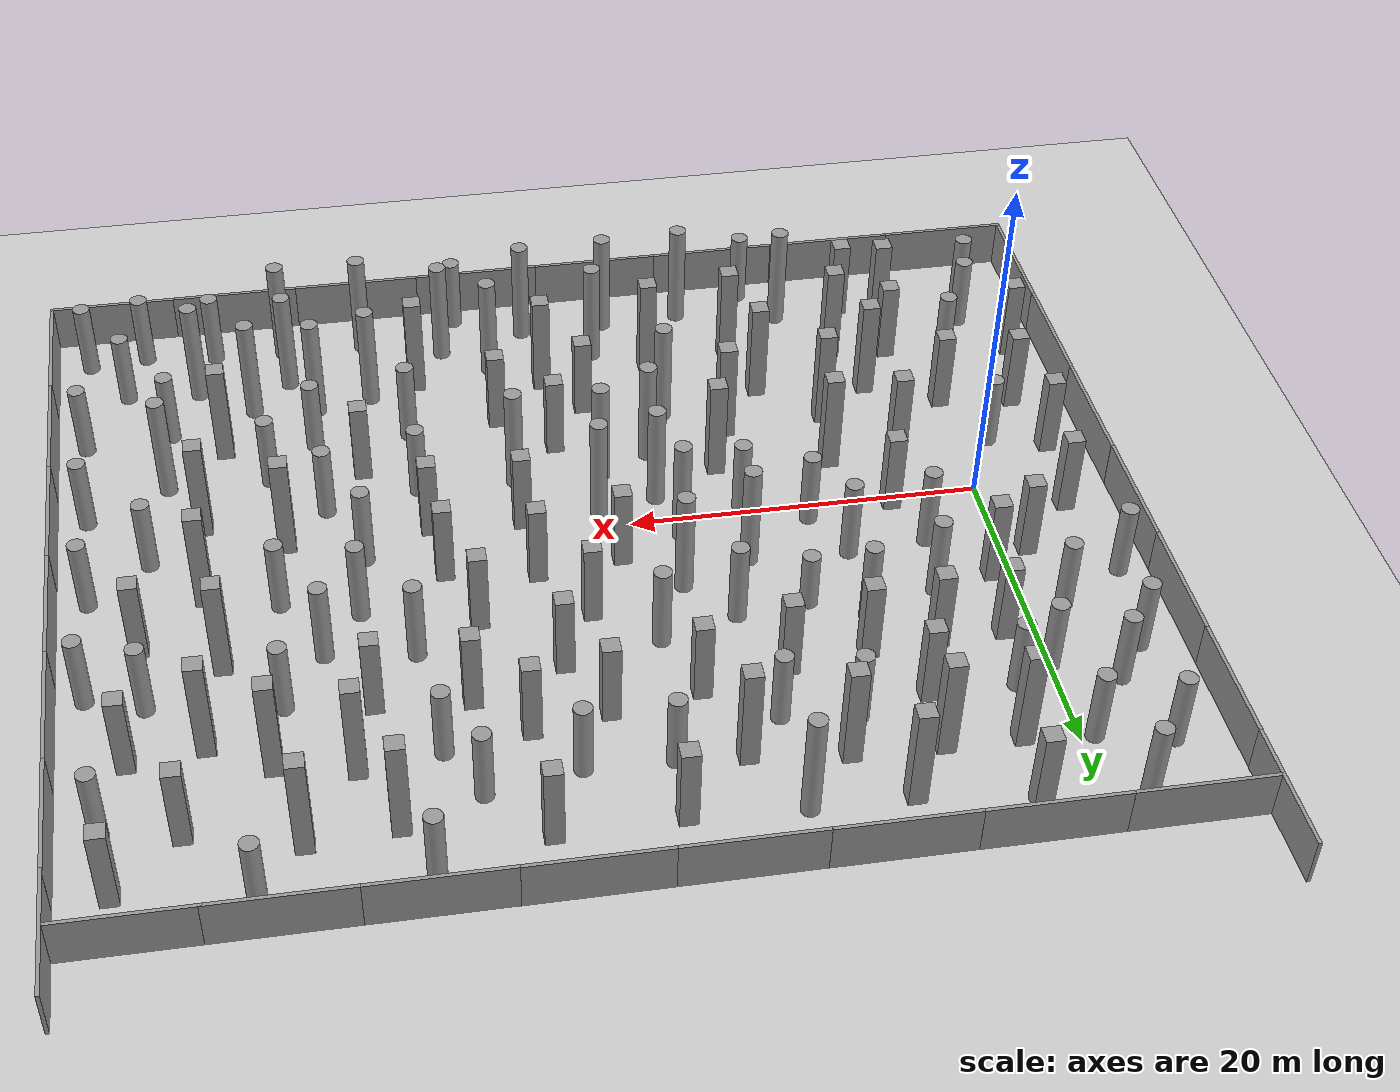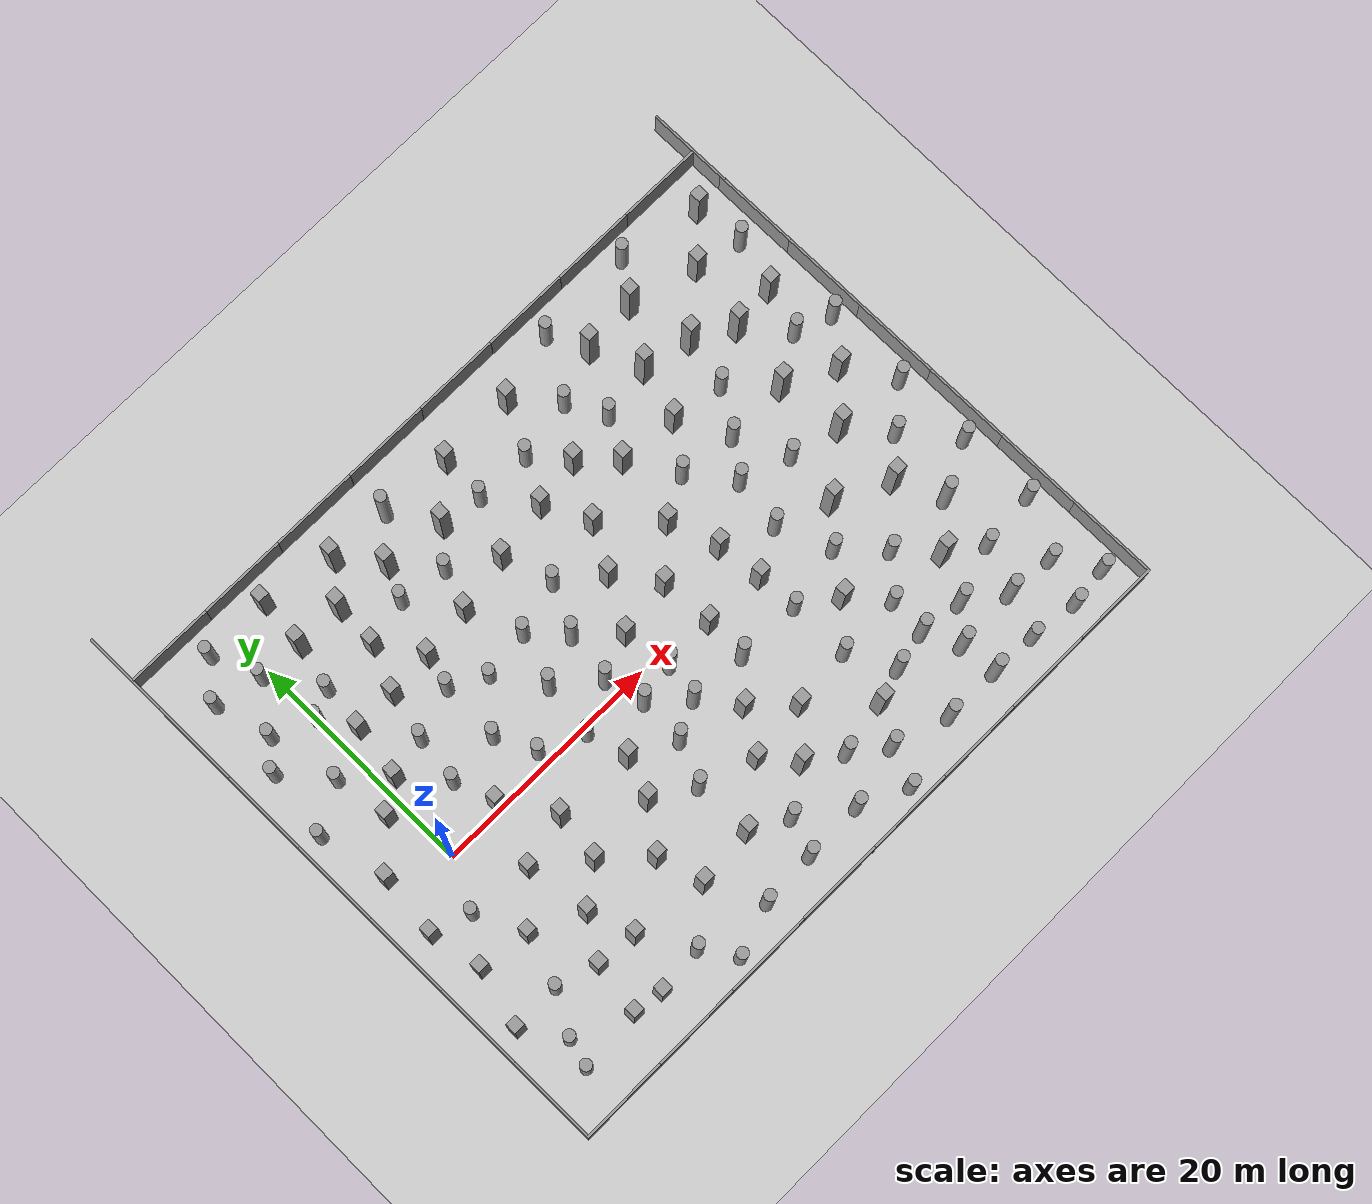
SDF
<sdf version="1.7">
 <world name="default">
  <light name="sun" type="directional">
   <pose>0 0 10 0 -0 0</pose>
   <diffuse>0.8 0.8 0.8 1</diffuse>
   <specular>0.2 0.2 0.2 1</specular>
   <attenuation>
    <range>1000</range>
    <constant>0.9</constant>
    <linear>0.01</linear>
    <quadratic>0.001</quadratic>
   </attenuation>
   <direction>-0.5 0.1 -0.9</direction>
   <spot><inner_angle>0</inner_angle><outer_angle>0</outer_angle><falloff>0</falloff></spot>
  </light>
  <model name="ground_plane">
   <static>1</static>
   <link name="link">
    <collision name="collision">
     <geometry><plane><normal>0 0 1</normal><size>400 400</size></plane></geometry>
     <surface><friction><ode><mu>100</mu><mu2>50</mu2></ode></friction></surface>
    </collision>
    <visual name="visual">
     <cast_shadows>0</cast_shadows>
     <geometry><plane><normal>0 0 1</normal><size>100 100</size></plane></geometry>
     <material>
      <script><uri>file://media/materials/scripts/gazebo.material</uri><name>Gazebo/Grey</name></script>
     </material>
    </visual>
   </link>
  </model>
  <gravity>0 0 -9.8</gravity>
  <magnetic_field>6e-06 2.3e-05 -4.2e-05</magnetic_field>
  <atmosphere type="adiabatic"/>
  <physics type="ode">
   <max_step_size>0.001</max_step_size>
   <real_time_factor>1</real_time_factor>
   <real_time_update_rate>1000</real_time_update_rate>
  </physics>
  <scene><ambient>0.4 0.4 0.4 1</ambient><background>0.7 0.7 0.7 1</background><shadows>1</shadows></scene>
  <spherical_coordinates>
   <surface_model>EARTH_WGS84</surface_model>
   <latitude_deg>0</latitude_deg>
   <longitude_deg>0</longitude_deg>
   <elevation>0</elevation>
   <heading_deg>0</heading_deg>
  </spherical_coordinates>
  <model name="unit_box_0">
   <pose>1.08465 7.15435 2.66138 2e-06 -0 -0.007188</pose>
   <link name="link">
    <inertial>
     <mass>1</mass>
     <inertia>
      <ixx>0.166667</ixx>
      <ixy>0</ixy>
      <ixz>0</ixz>
      <iyy>0.166667</iyy>
      <iyz>0</iyz>
      <izz>0.166667</izz>
     </inertia>
    </inertial>
    <collision name="collision"><geometry><box><size>1 1 5.32276</size></box></geometry></collision>
    <visual name="visual">
     <geometry><box><size>1 1 5.32276</size></box></geometry>
     <material>
      <script><name>Gazebo/Grey</name><uri>file://media/materials/scripts/gazebo.material</uri></script>
     </material>
    </visual>
   </link>
  </model>
  <model name="unit_cylinder_11">
   <pose>8.59291 9.34423 2.5135 2e-06 0 -0.000619</pose>
   <link name="link">
    <inertial>
     <mass>1</mass>
     <inertia><ixx>0.145833</ixx><ixy>0</ixy><ixz>0</ixz><iyy>0.145833</iyy><iyz>0</iyz><izz>0.125</izz></inertia>
    </inertial>
    <collision name="collision">
     <geometry><cylinder><radius>0.5</radius><length>5.02706</length></cylinder></geometry>
    </collision>
    <visual name="visual">
     <geometry><cylinder><radius>0.5</radius><length>5.02706</length></cylinder></geometry>
     <material>
      <script><name>Gazebo/Grey</name><uri>file://media/materials/scripts/gazebo.material</uri></script>
     </material>
    </visual>
   </link>
  </model>
  <model name="unit_cylinder_23">
   <pose>11.5428 7.81955 1.72625 1e-06 0 5.3e-05</pose>
   <link name="link">
    <inertial>
     <mass>1</mass>
     <inertia><ixx>0.145833</ixx><ixy>0</ixy><ixz>0</ixz><iyy>0.145833</iyy><iyz>0</iyz><izz>0.125</izz></inertia>
    </inertial>
    <collision name="collision">
     <geometry><cylinder><radius>0.5</radius><length>3.45257</length></cylinder></geometry>
    </collision>
    <visual name="visual">
     <geometry><cylinder><radius>0.5</radius><length>3.45257</length></cylinder></geometry>
     <material>
      <script><name>Gazebo/Grey</name><uri>file://media/materials/scripts/gazebo.material</uri></script>
     </material>
    </visual>
   </link>
  </model>
  <model name="unit_box_1_clone">
   <pose>1.75297 11.7119 2.48504 2e-06 -0 -0.005082</pose>
   <link name="link">
    <inertial>
     <mass>1</mass>
     <inertia>
      <ixx>0.166667</ixx>
      <ixy>0</ixy>
      <ixz>0</ixz>
      <iyy>0.166667</iyy>
      <iyz>0</iyz>
      <izz>0.166667</izz>
     </inertia>
    </inertial>
    <collision name="collision"><geometry><box><size>1 1 4.97009</size></box></geometry></collision>
    <visual name="visual">
     <geometry><box><size>1 1 4.97009</size></box></geometry>
     <material>
      <script><name>Gazebo/Grey</name><uri>file://media/materials/scripts/gazebo.material</uri></script>
     </material>
    </visual>
   </link>
  </model>
  <model name="unit_box_1_clone_0">
   <pose>5.37838 11.8011 2.48504 2e-06 -0 -0.002102</pose>
   <link name="link">
    <inertial>
     <mass>1</mass>
     <inertia>
      <ixx>0.166667</ixx>
      <ixy>0</ixy>
      <ixz>0</ixz>
      <iyy>0.166667</iyy>
      <iyz>0</iyz>
      <izz>0.166667</izz>
     </inertia>
    </inertial>
    <collision name="collision"><geometry><box><size>1 1 4.97009</size></box></geometry></collision>
    <visual name="visual">
     <geometry><box><size>1 1 4.97009</size></box></geometry>
     <material>
      <script><name>Gazebo/Grey</name><uri>file://media/materials/scripts/gazebo.material</uri></script>
     </material>
    </visual>
   </link>
  </model>
  <model name="unit_box_1_clone_1">
   <pose>9.26271 12.0297 2.48504 -0 2e-06 -0.00345</pose>
   <link name="link">
    <inertial>
     <mass>1</mass>
     <inertia>
      <ixx>0.166667</ixx>
      <ixy>0</ixy>
      <ixz>0</ixz>
      <iyy>0.166667</iyy>
      <iyz>0</iyz>
      <izz>0.166667</izz>
     </inertia>
    </inertial>
    <collision name="collision"><geometry><box><size>1 1 4.97009</size></box></geometry></collision>
    <visual name="visual">
     <geometry><box><size>1 1 4.97009</size></box></geometry>
     <material>
      <script><name>Gazebo/Grey</name><uri>file://media/materials/scripts/gazebo.material</uri></script>
     </material>
    </visual>
   </link>
  </model>
  <model name="unit_box_1_clone_2">
   <pose>13.6783 12.5927 2.48504 -2e-06 0 0.000428</pose>
   <link name="link">
    <inertial>
     <mass>1</mass>
     <inertia>
      <ixx>0.166667</ixx>
      <ixy>0</ixy>
      <ixz>0</ixz>
      <iyy>0.166667</iyy>
      <iyz>0</iyz>
      <izz>0.166667</izz>
     </inertia>
    </inertial>
    <collision name="collision"><geometry><box><size>1 1 4.97009</size></box></geometry></collision>
    <visual name="visual">
     <geometry><box><size>1 1 4.97009</size></box></geometry>
     <material>
      <script><name>Gazebo/Grey</name><uri>file://media/materials/scripts/gazebo.material</uri></script>
     </material>
    </visual>
   </link>
  </model>
  <model name="unit_box_1_clone_3">
   <pose>18.5455 13.5678 2.48504 -0 2e-06 -0.001973</pose>
   <link name="link">
    <inertial>
     <mass>1</mass>
     <inertia>
      <ixx>0.166667</ixx>
      <ixy>0</ixy>
      <ixz>0</ixz>
      <iyy>0.166667</iyy>
      <iyz>0</iyz>
      <izz>0.166667</izz>
     </inertia>
    </inertial>
    <collision name="collision"><geometry><box><size>1 1 4.97009</size></box></geometry></collision>
    <visual name="visual">
     <geometry><box><size>1 1 4.97009</size></box></geometry>
     <material>
      <script><name>Gazebo/Grey</name><uri>file://media/materials/scripts/gazebo.material</uri></script>
     </material>
    </visual>
   </link>
  </model>
  <model name="unit_box_1_clone_4">
   <pose>25.3258 10.5912 2.48504 2e-06 -0 8.3e-05</pose>
   <link name="link">
    <inertial>
     <mass>1</mass>
     <inertia>
      <ixx>0.166667</ixx>
      <ixy>0</ixy>
      <ixz>0</ixz>
      <iyy>0.166667</iyy>
      <iyz>0</iyz>
      <izz>0.166667</izz>
     </inertia>
    </inertial>
    <collision name="collision"><geometry><box><size>1 1 4.97009</size></box></geometry></collision>
    <visual name="visual">
     <geometry><box><size>1 1 4.97009</size></box></geometry>
     <material>
      <script><name>Gazebo/Grey</name><uri>file://media/materials/scripts/gazebo.material</uri></script>
     </material>
    </visual>
   </link>
  </model>
  <model name="unit_box_1_clone_5">
   <pose>23.4699 14.3709 2.48504 -0 2e-06 -0.000948</pose>
   <link name="link">
    <inertial>
     <mass>1</mass>
     <inertia>
      <ixx>0.166667</ixx>
      <ixy>0</ixy>
      <ixz>0</ixz>
      <iyy>0.166667</iyy>
      <iyz>0</iyz>
      <izz>0.166667</izz>
     </inertia>
    </inertial>
    <collision name="collision"><geometry><box><size>1 1 4.97009</size></box></geometry></collision>
    <visual name="visual">
     <geometry><box><size>1 1 4.97009</size></box></geometry>
     <material>
      <script><name>Gazebo/Grey</name><uri>file://media/materials/scripts/gazebo.material</uri></script>
     </material>
    </visual>
   </link>
  </model>
  <model name="unit_box_1_clone_6">
   <pose>30.3843 12.4735 2.48504 -2e-06 -0 -0.002073</pose>
   <link name="link">
    <inertial>
     <mass>1</mass>
     <inertia>
      <ixx>0.166667</ixx>
      <ixy>0</ixy>
      <ixz>0</ixz>
      <iyy>0.166667</iyy>
      <iyz>0</iyz>
      <izz>0.166667</izz>
     </inertia>
    </inertial>
    <collision name="collision"><geometry><box><size>1 1 4.97009</size></box></geometry></collision>
    <visual name="visual">
     <geometry><box><size>1 1 4.97009</size></box></geometry>
     <material>
      <script><name>Gazebo/Grey</name><uri>file://media/materials/scripts/gazebo.material</uri></script>
     </material>
    </visual>
   </link>
  </model>
  <model name="unit_box_1_clone_7">
   <pose>27.6522 15.0776 2.48504 -0 -2e-06 -0.002553</pose>
   <link name="link">
    <inertial>
     <mass>1</mass>
     <inertia>
      <ixx>0.166667</ixx>
      <ixy>0</ixy>
      <ixz>0</ixz>
      <iyy>0.166667</iyy>
      <iyz>0</iyz>
      <izz>0.166667</izz>
     </inertia>
    </inertial>
    <collision name="collision"><geometry><box><size>1 1 4.97009</size></box></geometry></collision>
    <visual name="visual">
     <geometry><box><size>1 1 4.97009</size></box></geometry>
     <material>
      <script><name>Gazebo/Grey</name><uri>file://media/materials/scripts/gazebo.material</uri></script>
     </material>
    </visual>
   </link>
  </model>
  <model name="unit_box_1_clone_8">
   <pose>35.4718 12.045 2.48504 2e-06 -0 0.000921</pose>
   <link name="link">
    <inertial>
     <mass>1</mass>
     <inertia>
      <ixx>0.166667</ixx>
      <ixy>0</ixy>
      <ixz>0</ixz>
      <iyy>0.166667</iyy>
      <iyz>0</iyz>
      <izz>0.166667</izz>
     </inertia>
    </inertial>
    <collision name="collision"><geometry><box><size>1 1 4.97009</size></box></geometry></collision>
    <visual name="visual">
     <geometry><box><size>1 1 4.97009</size></box></geometry>
     <material>
      <script><name>Gazebo/Grey</name><uri>file://media/materials/scripts/gazebo.material</uri></script>
     </material>
    </visual>
   </link>
  </model>
  <model name="unit_box_1_clone_9">
   <pose>6.92117 15.5806 2.48504 2e-06 -0 0.001536</pose>
   <link name="link">
    <inertial>
     <mass>1</mass>
     <inertia>
      <ixx>0.166667</ixx>
      <ixy>0</ixy>
      <ixz>0</ixz>
      <iyy>0.166667</iyy>
      <iyz>0</iyz>
      <izz>0.166667</izz>
     </inertia>
    </inertial>
    <collision name="collision"><geometry><box><size>1 1 4.97009</size></box></geometry></collision>
    <visual name="visual">
     <geometry><box><size>1 1 4.97009</size></box></geometry>
     <material>
      <script><name>Gazebo/Grey</name><uri>file://media/materials/scripts/gazebo.material</uri></script>
     </material>
    </visual>
   </link>
  </model>
  <model name="unit_cylinder_27_clone">
   <pose>14.8751 16.0271 2.257 2e-06 -0 -0.000756</pose>
   <link name="link">
    <inertial>
     <mass>1</mass>
     <inertia><ixx>0.145833</ixx><ixy>0</ixy><ixz>0</ixz><iyy>0.145833</iyy><iyz>0</iyz><izz>0.125</izz></inertia>
    </inertial>
    <collision name="collision">
     <geometry><cylinder><radius>0.5</radius><length>4.51407</length></cylinder></geometry>
    </collision>
    <visual name="visual">
     <geometry><cylinder><radius>0.5</radius><length>4.51407</length></cylinder></geometry>
     <material>
      <script><name>Gazebo/Grey</name><uri>file://media/materials/scripts/gazebo.material</uri></script>
     </material>
    </visual>
   </link>
  </model>
  <model name="unit_cylinder_27_clone_0">
   <pose>10.8319 16.6345 2.257 2e-06 -0 -0.00071</pose>
   <link name="link">
    <inertial>
     <mass>1</mass>
     <inertia><ixx>0.145833</ixx><ixy>0</ixy><ixz>0</ixz><iyy>0.145833</iyy><iyz>0</iyz><izz>0.125</izz></inertia>
    </inertial>
    <collision name="collision">
     <geometry><cylinder><radius>0.5</radius><length>4.51407</length></cylinder></geometry>
    </collision>
    <visual name="visual">
     <geometry><cylinder><radius>0.5</radius><length>4.51407</length></cylinder></geometry>
     <material>
      <script><name>Gazebo/Grey</name><uri>file://media/materials/scripts/gazebo.material</uri></script>
     </material>
    </visual>
   </link>
  </model>
  <model name="unit_cylinder_27_clone_1">
   <pose>20.7051 18.1973 2.257 2e-06 -0 -0.000715</pose>
   <link name="link">
    <inertial>
     <mass>1</mass>
     <inertia><ixx>0.145833</ixx><ixy>0</ixy><ixz>0</ixz><iyy>0.145833</iyy><iyz>0</iyz><izz>0.125</izz></inertia>
    </inertial>
    <collision name="collision">
     <geometry><cylinder><radius>0.5</radius><length>4.51407</length></cylinder></geometry>
    </collision>
    <visual name="visual">
     <geometry><cylinder><radius>0.5</radius><length>4.51407</length></cylinder></geometry>
     <material>
      <script><name>Gazebo/Grey</name><uri>file://media/materials/scripts/gazebo.material</uri></script>
     </material>
    </visual>
   </link>
  </model>
  <model name="unit_cylinder_27_clone_2">
   <pose>32.2373 15.8432 2.257 2e-06 0 -0.000722</pose>
   <link name="link">
    <inertial>
     <mass>1</mass>
     <inertia><ixx>0.145833</ixx><ixy>0</ixy><ixz>0</ixz><iyy>0.145833</iyy><iyz>0</iyz><izz>0.125</izz></inertia>
    </inertial>
    <collision name="collision">
     <geometry><cylinder><radius>0.5</radius><length>4.51407</length></cylinder></geometry>
    </collision>
    <visual name="visual">
     <geometry><cylinder><radius>0.5</radius><length>4.51407</length></cylinder></geometry>
     <material>
      <script><name>Gazebo/Grey</name><uri>file://media/materials/scripts/gazebo.material</uri></script>
     </material>
    </visual>
   </link>
  </model>
  <model name="unit_cylinder_27_clone_3">
   <pose>25.4299 18.0464 2.257 2e-06 0 -0.000741</pose>
   <link name="link">
    <inertial>
     <mass>1</mass>
     <inertia><ixx>0.145833</ixx><ixy>0</ixy><ixz>0</ixz><iyy>0.145833</iyy><iyz>0</iyz><izz>0.125</izz></inertia>
    </inertial>
    <collision name="collision">
     <geometry><cylinder><radius>0.5</radius><length>4.51407</length></cylinder></geometry>
    </collision>
    <visual name="visual">
     <geometry><cylinder><radius>0.5</radius><length>4.51407</length></cylinder></geometry>
     <material>
      <script><name>Gazebo/Grey</name><uri>file://media/materials/scripts/gazebo.material</uri></script>
     </material>
    </visual>
   </link>
  </model>
  <model name="unit_cylinder_27_clone_4">
   <pose>2.15827 15.6508 2.257 2e-06 -0 -0.000742</pose>
   <link name="link">
    <inertial>
     <mass>1</mass>
     <inertia><ixx>0.145833</ixx><ixy>0</ixy><ixz>0</ixz><iyy>0.145833</iyy><iyz>0</iyz><izz>0.125</izz></inertia>
    </inertial>
    <collision name="collision">
     <geometry><cylinder><radius>0.5</radius><length>4.51407</length></cylinder></geometry>
    </collision>
    <visual name="visual">
     <geometry><cylinder><radius>0.5</radius><length>4.51407</length></cylinder></geometry>
     <material>
      <script><name>Gazebo/Grey</name><uri>file://media/materials/scripts/gazebo.material</uri></script>
     </material>
    </visual>
   </link>
  </model>
  <model name="unit_cylinder_27_clone_5">
   <pose>30.5383 18.9927 2.257 2e-06 0 -0.000743</pose>
   <link name="link">
    <inertial>
     <mass>1</mass>
     <inertia><ixx>0.145833</ixx><ixy>0</ixy><ixz>0</ixz><iyy>0.145833</iyy><iyz>0</iyz><izz>0.125</izz></inertia>
    </inertial>
    <collision name="collision">
     <geometry><cylinder><radius>0.5</radius><length>4.51407</length></cylinder></geometry>
    </collision>
    <visual name="visual">
     <geometry><cylinder><radius>0.5</radius><length>4.51407</length></cylinder></geometry>
     <material>
      <script><name>Gazebo/Grey</name><uri>file://media/materials/scripts/gazebo.material</uri></script>
     </material>
    </visual>
   </link>
  </model>
  <model name="unit_cylinder_27_clone_6">
   <pose>40.0713 11.4687 2.257 2e-06 -0 -0.000727</pose>
   <link name="link">
    <inertial>
     <mass>1</mass>
     <inertia><ixx>0.145833</ixx><ixy>0</ixy><ixz>0</ixz><iyy>0.145833</iyy><iyz>0</iyz><izz>0.125</izz></inertia>
    </inertial>
    <collision name="collision">
     <geometry><cylinder><radius>0.5</radius><length>4.51407</length></cylinder></geometry>
    </collision>
    <visual name="visual">
     <geometry><cylinder><radius>0.5</radius><length>4.51407</length></cylinder></geometry>
     <material>
      <script><name>Gazebo/Grey</name><uri>file://media/materials/scripts/gazebo.material</uri></script>
     </material>
    </visual>
   </link>
  </model>
  <model name="unit_cylinder_27_clone_7">
   <pose>39.8766 3.70131 2.257 2e-06 0 -0.000729</pose>
   <link name="link">
    <inertial>
     <mass>1</mass>
     <inertia><ixx>0.145833</ixx><ixy>0</ixy><ixz>0</ixz><iyy>0.145833</iyy><iyz>0</iyz><izz>0.125</izz></inertia>
    </inertial>
    <collision name="collision">
     <geometry><cylinder><radius>0.5</radius><length>4.51407</length></cylinder></geometry>
    </collision>
    <visual name="visual">
     <geometry><cylinder><radius>0.5</radius><length>4.51407</length></cylinder></geometry>
     <material>
      <script><name>Gazebo/Grey</name><uri>file://media/materials/scripts/gazebo.material</uri></script>
     </material>
    </visual>
   </link>
  </model>
  <model name="unit_cylinder_27_clone_8">
   <pose>36.8795 -3.70449 2.257 2e-06 0 -0.000726</pose>
   <link name="link">
    <inertial>
     <mass>1</mass>
     <inertia><ixx>0.145833</ixx><ixy>0</ixy><ixz>0</ixz><iyy>0.145833</iyy><iyz>0</iyz><izz>0.125</izz></inertia>
    </inertial>
    <collision name="collision">
     <geometry><cylinder><radius>0.5</radius><length>4.51407</length></cylinder></geometry>
    </collision>
    <visual name="visual">
     <geometry><cylinder><radius>0.5</radius><length>4.51407</length></cylinder></geometry>
     <material>
      <script><name>Gazebo/Grey</name><uri>file://media/materials/scripts/gazebo.material</uri></script>
     </material>
    </visual>
   </link>
  </model>
  <model name="unit_cylinder_27_clone_9">
   <pose>37.1597 -9.74418 2.257 2e-06 -0 -0.000727</pose>
   <link name="link">
    <inertial>
     <mass>1</mass>
     <inertia><ixx>0.145833</ixx><ixy>0</ixy><ixz>0</ixz><iyy>0.145833</iyy><iyz>0</iyz><izz>0.125</izz></inertia>
    </inertial>
    <collision name="collision">
     <geometry><cylinder><radius>0.5</radius><length>4.51407</length></cylinder></geometry>
    </collision>
    <visual name="visual">
     <geometry><cylinder><radius>0.5</radius><length>4.51407</length></cylinder></geometry>
     <material>
      <script><name>Gazebo/Grey</name><uri>file://media/materials/scripts/gazebo.material</uri></script>
     </material>
    </visual>
   </link>
  </model>
  <model name="unit_cylinder_27_clone_10">
   <pose>31.5623 -4.75748 2.257 2e-06 0 -0.000706</pose>
   <link name="link">
    <inertial>
     <mass>1</mass>
     <inertia><ixx>0.145833</ixx><ixy>0</ixy><ixz>0</ixz><iyy>0.145833</iyy><iyz>0</iyz><izz>0.125</izz></inertia>
    </inertial>
    <collision name="collision">
     <geometry><cylinder><radius>0.5</radius><length>4.51407</length></cylinder></geometry>
    </collision>
    <visual name="visual">
     <geometry><cylinder><radius>0.5</radius><length>4.51407</length></cylinder></geometry>
     <material>
      <script><name>Gazebo/Grey</name><uri>file://media/materials/scripts/gazebo.material</uri></script>
     </material>
    </visual>
   </link>
  </model>
  <model name="unit_cylinder_27_clone_11">
   <pose>39.891 -6.87466 2.257 2e-06 -0 -0.000742</pose>
   <link name="link">
    <inertial>
     <mass>1</mass>
     <inertia><ixx>0.145833</ixx><ixy>0</ixy><ixz>0</ixz><iyy>0.145833</iyy><iyz>0</iyz><izz>0.125</izz></inertia>
    </inertial>
    <collision name="collision">
     <geometry><cylinder><radius>0.5</radius><length>4.51407</length></cylinder></geometry>
    </collision>
    <visual name="visual">
     <geometry><cylinder><radius>0.5</radius><length>4.51407</length></cylinder></geometry>
     <material>
      <script><name>Gazebo/Grey</name><uri>file://media/materials/scripts/gazebo.material</uri></script>
     </material>
    </visual>
   </link>
  </model>
  <model name="unit_box_8_clone">
   <pose>39.2587 -1.07295 3.10477 0 1e-06 -0.011993</pose>
   <link name="link">
    <inertial>
     <mass>1</mass>
     <inertia>
      <ixx>0.166667</ixx>
      <ixy>0</ixy>
      <ixz>0</ixz>
      <iyy>0.166667</iyy>
      <iyz>0</iyz>
      <izz>0.166667</izz>
     </inertia>
    </inertial>
    <collision name="collision"><geometry><box><size>1 1 6.20954</size></box></geometry></collision>
    <visual name="visual">
     <geometry><box><size>1 1 6.20954</size></box></geometry>
     <material>
      <script><name>Gazebo/Grey</name><uri>file://media/materials/scripts/gazebo.material</uri></script>
     </material>
    </visual>
   </link>
  </model>
  <model name="unit_box_8_clone_0">
   <pose>43.8059 -3.23967 3.10477 -2e-06 5e-06 -0.008215</pose>
   <link name="link">
    <inertial>
     <mass>1</mass>
     <inertia>
      <ixx>0.166667</ixx>
      <ixy>0</ixy>
      <ixz>0</ixz>
      <iyy>0.166667</iyy>
      <iyz>0</iyz>
      <izz>0.166667</izz>
     </inertia>
    </inertial>
    <collision name="collision"><geometry><box><size>1 1 6.20954</size></box></geometry></collision>
    <visual name="visual">
     <geometry><box><size>1 1 6.20954</size></box></geometry>
     <material>
      <script><name>Gazebo/Grey</name><uri>file://media/materials/scripts/gazebo.material</uri></script>
     </material>
    </visual>
   </link>
  </model>
  <model name="unit_box_8_clone_1">
   <pose>43.9322 2.54455 3.10477 -0 1e-06 -0.00839</pose>
   <link name="link">
    <inertial>
     <mass>1</mass>
     <inertia>
      <ixx>0.166667</ixx>
      <ixy>0</ixy>
      <ixz>0</ixz>
      <iyy>0.166667</iyy>
      <iyz>0</iyz>
      <izz>0.166667</izz>
     </inertia>
    </inertial>
    <collision name="collision"><geometry><box><size>1 1 6.20954</size></box></geometry></collision>
    <visual name="visual">
     <geometry><box><size>1 1 6.20954</size></box></geometry>
     <material>
      <script><name>Gazebo/Grey</name><uri>file://media/materials/scripts/gazebo.material</uri></script>
     </material>
    </visual>
   </link>
  </model>
  <model name="unit_box_8_clone_2">
   <pose>43.1123 8.00654 3.10477 2e-06 2e-06 -0.014033</pose>
   <link name="link">
    <inertial>
     <mass>1</mass>
     <inertia>
      <ixx>0.166667</ixx>
      <ixy>0</ixy>
      <ixz>0</ixz>
      <iyy>0.166667</iyy>
      <iyz>0</iyz>
      <izz>0.166667</izz>
     </inertia>
    </inertial>
    <collision name="collision"><geometry><box><size>1 1 6.20954</size></box></geometry></collision>
    <visual name="visual">
     <geometry><box><size>1 1 6.20954</size></box></geometry>
     <material>
      <script><name>Gazebo/Grey</name><uri>file://media/materials/scripts/gazebo.material</uri></script>
     </material>
    </visual>
   </link>
  </model>
  <model name="unit_box_8_clone_3">
   <pose>42.3824 -9.85764 3.10477 0 -1e-06 -0.007014</pose>
   <link name="link">
    <inertial>
     <mass>1</mass>
     <inertia>
      <ixx>0.166667</ixx>
      <ixy>0</ixy>
      <ixz>0</ixz>
      <iyy>0.166667</iyy>
      <iyz>0</iyz>
      <izz>0.166667</izz>
     </inertia>
    </inertial>
    <collision name="collision"><geometry><box><size>1 1 6.20954</size></box></geometry></collision>
    <visual name="visual">
     <geometry><box><size>1 1 6.20954</size></box></geometry>
     <material>
      <script><name>Gazebo/Grey</name><uri>file://media/materials/scripts/gazebo.material</uri></script>
     </material>
    </visual>
   </link>
  </model>
  <model name="unit_box_8_clone_4">
   <pose>36.6569 16.444 3.10477 0 -5e-06 -0.00826</pose>
   <link name="link">
    <inertial>
     <mass>1</mass>
     <inertia>
      <ixx>0.166667</ixx>
      <ixy>0</ixy>
      <ixz>0</ixz>
      <iyy>0.166667</iyy>
      <iyz>0</iyz>
      <izz>0.166667</izz>
     </inertia>
    </inertial>
    <collision name="collision"><geometry><box><size>1 1 6.20954</size></box></geometry></collision>
    <visual name="visual">
     <geometry><box><size>1 1 6.20954</size></box></geometry>
     <material>
      <script><name>Gazebo/Grey</name><uri>file://media/materials/scripts/gazebo.material</uri></script>
     </material>
    </visual>
   </link>
  </model>
  <model name="unit_box_8_clone_5">
   <pose>34.8228 20.5181 3.10477 1e-06 0 -0.007359</pose>
   <link name="link">
    <inertial>
     <mass>1</mass>
     <inertia>
      <ixx>0.166667</ixx>
      <ixy>0</ixy>
      <ixz>0</ixz>
      <iyy>0.166667</iyy>
      <iyz>0</iyz>
      <izz>0.166667</izz>
     </inertia>
    </inertial>
    <collision name="collision"><geometry><box><size>1 1 6.20954</size></box></geometry></collision>
    <visual name="visual">
     <geometry><box><size>1 1 6.20954</size></box></geometry>
     <material>
      <script><name>Gazebo/Grey</name><uri>file://media/materials/scripts/gazebo.material</uri></script>
     </material>
    </visual>
   </link>
  </model>
  <model name="unit_box_8_clone_6">
   <pose>40.8136 15.5915 3.10477 0 -1e-06 -0.005825</pose>
   <link name="link">
    <inertial>
     <mass>1</mass>
     <inertia>
      <ixx>0.166667</ixx>
      <ixy>0</ixy>
      <ixz>0</ixz>
      <iyy>0.166667</iyy>
      <iyz>0</iyz>
      <izz>0.166667</izz>
     </inertia>
    </inertial>
    <collision name="collision"><geometry><box><size>1 1 6.20954</size></box></geometry></collision>
    <visual name="visual">
     <geometry><box><size>1 1 6.20954</size></box></geometry>
     <material>
      <script><name>Gazebo/Grey</name><uri>file://media/materials/scripts/gazebo.material</uri></script>
     </material>
    </visual>
   </link>
  </model>
  <model name="unit_box_8_clone_7">
   <pose>39.5843 20.9218 3.10477 -0 1e-06 -0.008927</pose>
   <link name="link">
    <inertial>
     <mass>1</mass>
     <inertia>
      <ixx>0.166667</ixx>
      <ixy>0</ixy>
      <ixz>0</ixz>
      <iyy>0.166667</iyy>
      <iyz>0</iyz>
      <izz>0.166667</izz>
     </inertia>
    </inertial>
    <collision name="collision"><geometry><box><size>1 1 6.20954</size></box></geometry></collision>
    <visual name="visual">
     <geometry><box><size>1 1 6.20954</size></box></geometry>
     <material>
      <script><name>Gazebo/Grey</name><uri>file://media/materials/scripts/gazebo.material</uri></script>
     </material>
    </visual>
   </link>
  </model>
  <model name="unit_box_8_clone_8">
   <pose>44.1425 13.7168 3.10477 1e-06 -0 -0.009169</pose>
   <link name="link">
    <inertial>
     <mass>1</mass>
     <inertia>
      <ixx>0.166667</ixx>
      <ixy>0</ixy>
      <ixz>0</ixz>
      <iyy>0.166667</iyy>
      <iyz>0</iyz>
      <izz>0.166667</izz>
     </inertia>
    </inertial>
    <collision name="collision"><geometry><box><size>1 1 6.20954</size></box></geometry></collision>
    <visual name="visual">
     <geometry><box><size>1 1 6.20954</size></box></geometry>
     <material>
      <script><name>Gazebo/Grey</name><uri>file://media/materials/scripts/gazebo.material</uri></script>
     </material>
    </visual>
   </link>
  </model>
  <model name="unit_box_8_clone_9">
   <pose>17.0789 18.4775 3.10477 0 -1e-06 -0.010304</pose>
   <link name="link">
    <inertial>
     <mass>1</mass>
     <inertia>
      <ixx>0.166667</ixx>
      <ixy>0</ixy>
      <ixz>0</ixz>
      <iyy>0.166667</iyy>
      <iyz>0</iyz>
      <izz>0.166667</izz>
     </inertia>
    </inertial>
    <collision name="collision"><geometry><box><size>1 1 6.20954</size></box></geometry></collision>
    <visual name="visual">
     <geometry><box><size>1 1 6.20954</size></box></geometry>
     <material>
      <script><name>Gazebo/Grey</name><uri>file://media/materials/scripts/gazebo.material</uri></script>
     </material>
    </visual>
   </link>
  </model>
  <model name="unit_box_8_clone_10">
   <pose>11.9286 19.1593 3.10477 -0 5e-06 -0.00807</pose>
   <link name="link">
    <inertial>
     <mass>1</mass>
     <inertia>
      <ixx>0.166667</ixx>
      <ixy>0</ixy>
      <ixz>0</ixz>
      <iyy>0.166667</iyy>
      <iyz>0</iyz>
      <izz>0.166667</izz>
     </inertia>
    </inertial>
    <collision name="collision"><geometry><box><size>1 1 6.20954</size></box></geometry></collision>
    <visual name="visual">
     <geometry><box><size>1 1 6.20954</size></box></geometry>
     <material>
      <script><name>Gazebo/Grey</name><uri>file://media/materials/scripts/gazebo.material</uri></script>
     </material>
    </visual>
   </link>
  </model>
  <model name="unit_box_8_clone_11">
   <pose>7.04757 19.3025 3.10477 0 1e-06 -0.00742</pose>
   <link name="link">
    <inertial>
     <mass>1</mass>
     <inertia>
      <ixx>0.166667</ixx>
      <ixy>0</ixy>
      <ixz>0</ixz>
      <iyy>0.166667</iyy>
      <iyz>0</iyz>
      <izz>0.166667</izz>
     </inertia>
    </inertial>
    <collision name="collision"><geometry><box><size>1 1 6.20954</size></box></geometry></collision>
    <visual name="visual">
     <geometry><box><size>1 1 6.20954</size></box></geometry>
     <material>
      <script><name>Gazebo/Grey</name><uri>file://media/materials/scripts/gazebo.material</uri></script>
     </material>
    </visual>
   </link>
  </model>
  <model name="unit_box_8_clone_12">
   <pose>2.9683 19.3773 3.10477 1e-06 0 -0.009439</pose>
   <link name="link">
    <inertial>
     <mass>1</mass>
     <inertia>
      <ixx>0.166667</ixx>
      <ixy>0</ixy>
      <ixz>0</ixz>
      <iyy>0.166667</iyy>
      <iyz>0</iyz>
      <izz>0.166667</izz>
     </inertia>
    </inertial>
    <collision name="collision"><geometry><box><size>1 1 6.20954</size></box></geometry></collision>
    <visual name="visual">
     <geometry><box><size>1 1 6.20954</size></box></geometry>
     <material>
      <script><name>Gazebo/Grey</name><uri>file://media/materials/scripts/gazebo.material</uri></script>
     </material>
    </visual>
   </link>
  </model>
  <model name="unit_box_8_clone_13">
   <pose>9.37041 22.3926 3.10477 -1e-06 -0 -0.009041</pose>
   <link name="link">
    <inertial>
     <mass>1</mass>
     <inertia>
      <ixx>0.166667</ixx>
      <ixy>0</ixy>
      <ixz>0</ixz>
      <iyy>0.166667</iyy>
      <iyz>0</iyz>
      <izz>0.166667</izz>
     </inertia>
    </inertial>
    <collision name="collision"><geometry><box><size>1 1 6.20954</size></box></geometry></collision>
    <visual name="visual">
     <geometry><box><size>1 1 6.20954</size></box></geometry>
     <material>
      <script><name>Gazebo/Grey</name><uri>file://media/materials/scripts/gazebo.material</uri></script>
     </material>
    </visual>
   </link>
  </model>
  <model name="unit_box_8_clone_14">
   <pose>5.41114 -13.8377 3.10477 -2e-06 5e-06 -0.007905</pose>
   <link name="link">
    <inertial>
     <mass>1</mass>
     <inertia>
      <ixx>0.166667</ixx>
      <ixy>0</ixy>
      <ixz>0</ixz>
      <iyy>0.166667</iyy>
      <iyz>0</iyz>
      <izz>0.166667</izz>
     </inertia>
    </inertial>
    <collision name="collision"><geometry><box><size>1 1 6.20954</size></box></geometry></collision>
    <visual name="visual">
     <geometry><box><size>1 1 6.20954</size></box></geometry>
     <material>
      <script><name>Gazebo/Grey</name><uri>file://media/materials/scripts/gazebo.material</uri></script>
     </material>
    </visual>
   </link>
  </model>
  <model name="unit_box_8_clone_15">
   <pose>11.6994 -14.7229 3.10477 0 -5e-06 -0.008049</pose>
   <link name="link">
    <inertial>
     <mass>1</mass>
     <inertia>
      <ixx>0.166667</ixx>
      <ixy>0</ixy>
      <ixz>0</ixz>
      <iyy>0.166667</iyy>
      <iyz>0</iyz>
      <izz>0.166667</izz>
     </inertia>
    </inertial>
    <collision name="collision"><geometry><box><size>1 1 6.20954</size></box></geometry></collision>
    <visual name="visual">
     <geometry><box><size>1 1 6.20954</size></box></geometry>
     <material>
      <script><name>Gazebo/Grey</name><uri>file://media/materials/scripts/gazebo.material</uri></script>
     </material>
    </visual>
   </link>
  </model>
  <model name="unit_box_8_clone_16">
   <pose>16.7136 -14.2873 3.10477 2e-06 -5e-06 -0.009424</pose>
   <link name="link">
    <inertial>
     <mass>1</mass>
     <inertia>
      <ixx>0.166667</ixx>
      <ixy>0</ixy>
      <ixz>0</ixz>
      <iyy>0.166667</iyy>
      <iyz>0</iyz>
      <izz>0.166667</izz>
     </inertia>
    </inertial>
    <collision name="collision"><geometry><box><size>1 1 6.20954</size></box></geometry></collision>
    <visual name="visual">
     <geometry><box><size>1 1 6.20954</size></box></geometry>
     <material>
      <script><name>Gazebo/Grey</name><uri>file://media/materials/scripts/gazebo.material</uri></script>
     </material>
    </visual>
   </link>
  </model>
  <model name="unit_box_8_clone_17">
   <pose>23.2821 -13.5423 3.10477 1e-06 0 -0.007486</pose>
   <link name="link">
    <inertial>
     <mass>1</mass>
     <inertia>
      <ixx>0.166667</ixx>
      <ixy>0</ixy>
      <ixz>0</ixz>
      <iyy>0.166667</iyy>
      <iyz>0</iyz>
      <izz>0.166667</izz>
     </inertia>
    </inertial>
    <collision name="collision"><geometry><box><size>1 1 6.20954</size></box></geometry></collision>
    <visual name="visual">
     <geometry><box><size>1 1 6.20954</size></box></geometry>
     <material>
      <script><name>Gazebo/Grey</name><uri>file://media/materials/scripts/gazebo.material</uri></script>
     </material>
    </visual>
   </link>
  </model>
  <model name="unit_box_8_clone_18">
   <pose>30.7532 -14.5438 3.10477 2e-06 -5e-06 -0.009418</pose>
   <link name="link">
    <inertial>
     <mass>1</mass>
     <inertia>
      <ixx>0.166667</ixx>
      <ixy>0</ixy>
      <ixz>0</ixz>
      <iyy>0.166667</iyy>
      <iyz>0</iyz>
      <izz>0.166667</izz>
     </inertia>
    </inertial>
    <collision name="collision"><geometry><box><size>1 1 6.20954</size></box></geometry></collision>
    <visual name="visual">
     <geometry><box><size>1 1 6.20954</size></box></geometry>
     <material>
      <script><name>Gazebo/Grey</name><uri>file://media/materials/scripts/gazebo.material</uri></script>
     </material>
    </visual>
   </link>
  </model>
  <model name="unit_cylinder_17_clone">
   <pose>7.91046 -17.8277 3.23034 3e-06 -1e-06 0.007131</pose>
   <link name="link">
    <inertial>
     <mass>1</mass>
     <inertia><ixx>0.145833</ixx><ixy>0</ixy><ixz>0</ixz><iyy>0.145833</iyy><iyz>0</iyz><izz>0.125</izz></inertia>
    </inertial>
    <collision name="collision">
     <geometry><cylinder><radius>0.5</radius><length>6.46075</length></cylinder></geometry>
    </collision>
    <visual name="visual">
     <geometry><cylinder><radius>0.5</radius><length>6.46075</length></cylinder></geometry>
     <material>
      <script><name>Gazebo/Grey</name><uri>file://media/materials/scripts/gazebo.material</uri></script>
     </material>
    </visual>
   </link>
  </model>
  <model name="unit_cylinder_17_clone_0">
   <pose>26.1992 -15.3901 3.23034 3e-06 -1e-06 0.007121</pose>
   <link name="link">
    <inertial>
     <mass>1</mass>
     <inertia><ixx>0.145833</ixx><ixy>0</ixy><ixz>0</ixz><iyy>0.145833</iyy><iyz>0</iyz><izz>0.125</izz></inertia>
    </inertial>
    <collision name="collision">
     <geometry><cylinder><radius>0.5</radius><length>6.46075</length></cylinder></geometry>
    </collision>
    <visual name="visual">
     <geometry><cylinder><radius>0.5</radius><length>6.46075</length></cylinder></geometry>
     <material>
      <script><name>Gazebo/Grey</name><uri>file://media/materials/scripts/gazebo.material</uri></script>
     </material>
    </visual>
   </link>
  </model>
  <model name="unit_cylinder_17_clone_1">
   <pose>19.8231 -15.8838 3.23034 3e-06 -1e-06 0.007124</pose>
   <link name="link">
    <inertial>
     <mass>1</mass>
     <inertia><ixx>0.145833</ixx><ixy>0</ixy><ixz>0</ixz><iyy>0.145833</iyy><iyz>0</iyz><izz>0.125</izz></inertia>
    </inertial>
    <collision name="collision">
     <geometry><cylinder><radius>0.5</radius><length>6.46075</length></cylinder></geometry>
    </collision>
    <visual name="visual">
     <geometry><cylinder><radius>0.5</radius><length>6.46075</length></cylinder></geometry>
     <material>
      <script><name>Gazebo/Grey</name><uri>file://media/materials/scripts/gazebo.material</uri></script>
     </material>
    </visual>
   </link>
  </model>
  <model name="unit_cylinder_17_clone_3">
   <pose>40.5461 -13.4182 3.23034 3e-06 -1e-06 0.007107</pose>
   <link name="link">
    <inertial>
     <mass>1</mass>
     <inertia><ixx>0.145833</ixx><ixy>0</ixy><ixz>0</ixz><iyy>0.145833</iyy><iyz>0</iyz><izz>0.125</izz></inertia>
    </inertial>
    <collision name="collision">
     <geometry><cylinder><radius>0.5</radius><length>6.46075</length></cylinder></geometry>
    </collision>
    <visual name="visual">
     <geometry><cylinder><radius>0.5</radius><length>6.46075</length></cylinder></geometry>
     <material>
      <script><name>Gazebo/Grey</name><uri>file://media/materials/scripts/gazebo.material</uri></script>
     </material>
    </visual>
   </link>
  </model>
  <model name="unit_cylinder_17_clone_4">
   <pose>14.0195 -19.0586 3.23034 3e-06 -1e-06 0.007104</pose>
   <link name="link">
    <inertial>
     <mass>1</mass>
     <inertia><ixx>0.145833</ixx><ixy>0</ixy><ixz>0</ixz><iyy>0.145833</iyy><iyz>0</iyz><izz>0.125</izz></inertia>
    </inertial>
    <collision name="collision">
     <geometry><cylinder><radius>0.5</radius><length>6.46075</length></cylinder></geometry>
    </collision>
    <visual name="visual">
     <geometry><cylinder><radius>0.5</radius><length>6.46075</length></cylinder></geometry>
     <material>
      <script><name>Gazebo/Grey</name><uri>file://media/materials/scripts/gazebo.material</uri></script>
     </material>
    </visual>
   </link>
  </model>
  <model name="unit_cylinder_17_clone_5">
   <pose>18.7577 -18.835 3.23034 3e-06 -1e-06 0.007073</pose>
   <link name="link">
    <inertial>
     <mass>1</mass>
     <inertia><ixx>0.145833</ixx><ixy>0</ixy><ixz>0</ixz><iyy>0.145833</iyy><iyz>0</iyz><izz>0.125</izz></inertia>
    </inertial>
    <collision name="collision">
     <geometry><cylinder><radius>0.5</radius><length>6.46075</length></cylinder></geometry>
    </collision>
    <visual name="visual">
     <geometry><cylinder><radius>0.5</radius><length>6.46075</length></cylinder></geometry>
     <material>
      <script><name>Gazebo/Grey</name><uri>file://media/materials/scripts/gazebo.material</uri></script>
     </material>
    </visual>
   </link>
  </model>
  <model name="unit_cylinder_17_clone_6">
   <pose>23.8153 -18.7641 3.23034 3e-06 -1e-06 0.007075</pose>
   <link name="link">
    <inertial>
     <mass>1</mass>
     <inertia><ixx>0.145833</ixx><ixy>0</ixy><ixz>0</ixz><iyy>0.145833</iyy><iyz>0</iyz><izz>0.125</izz></inertia>
    </inertial>
    <collision name="collision">
     <geometry><cylinder><radius>0.5</radius><length>6.46075</length></cylinder></geometry>
    </collision>
    <visual name="visual">
     <geometry><cylinder><radius>0.5</radius><length>6.46075</length></cylinder></geometry>
     <material>
      <script><name>Gazebo/Grey</name><uri>file://media/materials/scripts/gazebo.material</uri></script>
     </material>
    </visual>
   </link>
  </model>
  <model name="unit_cylinder_17_clone_7">
   <pose>28.9284 -17.4482 3.23034 3e-06 -1e-06 0.00708</pose>
   <link name="link">
    <inertial>
     <mass>1</mass>
     <inertia><ixx>0.145833</ixx><ixy>0</ixy><ixz>0</ixz><iyy>0.145833</iyy><iyz>0</iyz><izz>0.125</izz></inertia>
    </inertial>
    <collision name="collision">
     <geometry><cylinder><radius>0.5</radius><length>6.46075</length></cylinder></geometry>
    </collision>
    <visual name="visual">
     <geometry><cylinder><radius>0.5</radius><length>6.46075</length></cylinder></geometry>
     <material>
      <script><name>Gazebo/Grey</name><uri>file://media/materials/scripts/gazebo.material</uri></script>
     </material>
    </visual>
   </link>
  </model>
  <model name="unit_cylinder_17_clone_8">
   <pose>33.688 -18.8972 3.23034 3e-06 -1e-06 0.007062</pose>
   <link name="link">
    <inertial>
     <mass>1</mass>
     <inertia><ixx>0.145833</ixx><ixy>0</ixy><ixz>0</ixz><iyy>0.145833</iyy><iyz>0</iyz><izz>0.125</izz></inertia>
    </inertial>
    <collision name="collision">
     <geometry><cylinder><radius>0.5</radius><length>6.46075</length></cylinder></geometry>
    </collision>
    <visual name="visual">
     <geometry><cylinder><radius>0.5</radius><length>6.46075</length></cylinder></geometry>
     <material>
      <script><name>Gazebo/Grey</name><uri>file://media/materials/scripts/gazebo.material</uri></script>
     </material>
    </visual>
   </link>
  </model>
  <model name="unit_cylinder_17_clone_9">
   <pose>33.5789 -13.6377 3.23034 3e-06 -1e-06 0.007064</pose>
   <link name="link">
    <inertial>
     <mass>1</mass>
     <inertia><ixx>0.145833</ixx><ixy>0</ixy><ixz>0</ixz><iyy>0.145833</iyy><iyz>0</iyz><izz>0.125</izz></inertia>
    </inertial>
    <collision name="collision">
     <geometry><cylinder><radius>0.5</radius><length>6.46075</length></cylinder></geometry>
    </collision>
    <visual name="visual">
     <geometry><cylinder><radius>0.5</radius><length>6.46075</length></cylinder></geometry>
     <material>
      <script><name>Gazebo/Grey</name><uri>file://media/materials/scripts/gazebo.material</uri></script>
     </material>
    </visual>
   </link>
  </model>
  <model name="unit_cylinder_17_clone_10">
   <pose>38.3088 -15.8097 3.23034 3e-06 -1e-06 0.007047</pose>
   <link name="link">
    <inertial>
     <mass>1</mass>
     <inertia><ixx>0.145833</ixx><ixy>0</ixy><ixz>0</ixz><iyy>0.145833</iyy><iyz>0</iyz><izz>0.125</izz></inertia>
    </inertial>
    <collision name="collision">
     <geometry><cylinder><radius>0.5</radius><length>6.46075</length></cylinder></geometry>
    </collision>
    <visual name="visual">
     <geometry><cylinder><radius>0.5</radius><length>6.46075</length></cylinder></geometry>
     <material>
      <script><name>Gazebo/Grey</name><uri>file://media/materials/scripts/gazebo.material</uri></script>
     </material>
    </visual>
   </link>
  </model>
  <model name="unit_cylinder_17_clone_2">
   <pose>36.8202 -12.9403 3.23034 3e-06 -1e-06 0.007012</pose>
   <link name="link">
    <inertial>
     <mass>1</mass>
     <inertia><ixx>0.145833</ixx><ixy>0</ixy><ixz>0</ixz><iyy>0.145833</iyy><iyz>0</iyz><izz>0.125</izz></inertia>
    </inertial>
    <collision name="collision">
     <geometry><cylinder><radius>0.5</radius><length>6.46075</length></cylinder></geometry>
    </collision>
    <visual name="visual">
     <geometry><cylinder><radius>0.5</radius><length>6.46075</length></cylinder></geometry>
     <material>
      <script><name>Gazebo/Grey</name><uri>file://media/materials/scripts/gazebo.material</uri></script>
     </material>
    </visual>
   </link>
  </model>
  <model name="unit_cylinder_17_clone_11">
   <pose>38.5353 -18.9509 3.23034 3e-06 -1e-06 0.00717</pose>
   <link name="link">
    <inertial>
     <mass>1</mass>
     <inertia><ixx>0.145833</ixx><ixy>0</ixy><ixz>0</ixz><iyy>0.145833</iyy><iyz>0</iyz><izz>0.125</izz></inertia>
    </inertial>
    <collision name="collision">
     <geometry><cylinder><radius>0.5</radius><length>6.46075</length></cylinder></geometry>
    </collision>
    <visual name="visual">
     <geometry><cylinder><radius>0.5</radius><length>6.46075</length></cylinder></geometry>
     <material>
      <script><name>Gazebo/Grey</name><uri>file://media/materials/scripts/gazebo.material</uri></script>
     </material>
    </visual>
   </link>
  </model>
  <model name="unit_cylinder_17_clone_12">
   <pose>43.7372 -15.5968 3.23034 3e-06 -1e-06 0.007173</pose>
   <link name="link">
    <inertial>
     <mass>1</mass>
     <inertia><ixx>0.145833</ixx><ixy>0</ixy><ixz>0</ixz><iyy>0.145833</iyy><iyz>0</iyz><izz>0.125</izz></inertia>
    </inertial>
    <collision name="collision">
     <geometry><cylinder><radius>0.5</radius><length>6.46075</length></cylinder></geometry>
    </collision>
    <visual name="visual">
     <geometry><cylinder><radius>0.5</radius><length>6.46075</length></cylinder></geometry>
     <material>
      <script><name>Gazebo/Grey</name><uri>file://media/materials/scripts/gazebo.material</uri></script>
     </material>
    </visual>
   </link>
  </model>
  <model name="unit_cylinder_17_clone_13">
   <pose>45.7275 -6.98851 3.23034 3e-06 -1e-06 0.007178</pose>
   <link name="link">
    <inertial>
     <mass>1</mass>
     <inertia><ixx>0.145833</ixx><ixy>0</ixy><ixz>0</ixz><iyy>0.145833</iyy><iyz>0</iyz><izz>0.125</izz></inertia>
    </inertial>
    <collision name="collision">
     <geometry><cylinder><radius>0.5</radius><length>6.46075</length></cylinder></geometry>
    </collision>
    <visual name="visual">
     <geometry><cylinder><radius>0.5</radius><length>6.46075</length></cylinder></geometry>
     <material>
      <script><name>Gazebo/Grey</name><uri>file://media/materials/scripts/gazebo.material</uri></script>
     </material>
    </visual>
   </link>
  </model>
  <model name="unit_cylinder_17_clone_14">
   <pose>25.9964 -4.68182 3.23034 3e-06 -1e-06 0.007158</pose>
   <link name="link">
    <inertial>
     <mass>1</mass>
     <inertia><ixx>0.145833</ixx><ixy>0</ixy><ixz>0</ixz><iyy>0.145833</iyy><iyz>0</iyz><izz>0.125</izz></inertia>
    </inertial>
    <collision name="collision">
     <geometry><cylinder><radius>0.5</radius><length>6.46075</length></cylinder></geometry>
    </collision>
    <visual name="visual">
     <geometry><cylinder><radius>0.5</radius><length>6.46075</length></cylinder></geometry>
     <material>
      <script><name>Gazebo/Grey</name><uri>file://media/materials/scripts/gazebo.material</uri></script>
     </material>
    </visual>
   </link>
  </model>
  <model name="unit_cylinder_17_clone_15">
   <pose>14.7277 22.4029 3.23034 3e-06 -1e-06 0.00718</pose>
   <link name="link">
    <inertial>
     <mass>1</mass>
     <inertia><ixx>0.145833</ixx><ixy>0</ixy><ixz>0</ixz><iyy>0.145833</iyy><iyz>0</iyz><izz>0.125</izz></inertia>
    </inertial>
    <collision name="collision">
     <geometry><cylinder><radius>0.5</radius><length>6.46075</length></cylinder></geometry>
    </collision>
    <visual name="visual">
     <geometry><cylinder><radius>0.5</radius><length>6.46075</length></cylinder></geometry>
     <material>
      <script><name>Gazebo/Grey</name><uri>file://media/materials/scripts/gazebo.material</uri></script>
     </material>
    </visual>
   </link>
  </model>
  <model name="unit_box_1_clone_3_clone">
   <pose>20.8351 21.999 2.48504 0 2e-06 -0.000957</pose>
   <link name="link">
    <inertial>
     <mass>1</mass>
     <inertia>
      <ixx>0.166667</ixx>
      <ixy>0</ixy>
      <ixz>0</ixz>
      <iyy>0.166667</iyy>
      <iyz>0</iyz>
      <izz>0.166667</izz>
     </inertia>
    </inertial>
    <collision name="collision"><geometry><box><size>1 1 4.97009</size></box></geometry></collision>
    <visual name="visual">
     <geometry><box><size>1 1 4.97009</size></box></geometry>
     <material>
      <script><name>Gazebo/Grey</name><uri>file://media/materials/scripts/gazebo.material</uri></script>
     </material>
    </visual>
   </link>
  </model>
  <model name="unit_box_1_clone_3_clone_0">
   <pose>27.5127 22.1575 2.48504 2e-06 0 -0.004486</pose>
   <link name="link">
    <inertial>
     <mass>1</mass>
     <inertia>
      <ixx>0.166667</ixx>
      <ixy>0</ixy>
      <ixz>0</ixz>
      <iyy>0.166667</iyy>
      <iyz>0</iyz>
      <izz>0.166667</izz>
     </inertia>
    </inertial>
    <collision name="collision"><geometry><box><size>1 1 4.97009</size></box></geometry></collision>
    <visual name="visual">
     <geometry><box><size>1 1 4.97009</size></box></geometry>
     <material>
      <script><name>Gazebo/Grey</name><uri>file://media/materials/scripts/gazebo.material</uri></script>
     </material>
    </visual>
   </link>
  </model>
  <model name="unit_box_1_clone_3_clone_1">
   <pose>45.4529 19.4287 2.48504 2e-06 -0 -0.002299</pose>
   <link name="link">
    <inertial>
     <mass>1</mass>
     <inertia>
      <ixx>0.166667</ixx>
      <ixy>0</ixy>
      <ixz>0</ixz>
      <iyy>0.166667</iyy>
      <iyz>0</iyz>
      <izz>0.166667</izz>
     </inertia>
    </inertial>
    <collision name="collision"><geometry><box><size>1 1 4.97009</size></box></geometry></collision>
    <visual name="visual">
     <geometry><box><size>1 1 4.97009</size></box></geometry>
     <material>
      <script><name>Gazebo/Grey</name><uri>file://media/materials/scripts/gazebo.material</uri></script>
     </material>
    </visual>
   </link>
  </model>
  <model name="unit_box_1_clone_3_clone_2">
   <pose>3.3198 23.7269 2.48504 2e-06 0 -0.004656</pose>
   <link name="link">
    <inertial>
     <mass>1</mass>
     <inertia>
      <ixx>0.166667</ixx>
      <ixy>0</ixy>
      <ixz>0</ixz>
      <iyy>0.166667</iyy>
      <iyz>0</iyz>
      <izz>0.166667</izz>
     </inertia>
    </inertial>
    <collision name="collision"><geometry><box><size>1 1 4.97009</size></box></geometry></collision>
    <visual name="visual">
     <geometry><box><size>1 1 4.97009</size></box></geometry>
     <material>
      <script><name>Gazebo/Grey</name><uri>file://media/materials/scripts/gazebo.material</uri></script>
     </material>
    </visual>
   </link>
  </model>
  <model name="unit_box_1_clone_3_clone_3">
   <pose>2.01116 -13.4762 2.48504 -0 -2e-06 0.000723</pose>
   <link name="link">
    <inertial>
     <mass>1</mass>
     <inertia>
      <ixx>0.166667</ixx>
      <ixy>0</ixy>
      <ixz>0</ixz>
      <iyy>0.166667</iyy>
      <iyz>0</iyz>
      <izz>0.166667</izz>
     </inertia>
    </inertial>
    <collision name="collision"><geometry><box><size>1 1 4.97009</size></box></geometry></collision>
    <visual name="visual">
     <geometry><box><size>1 1 4.97009</size></box></geometry>
     <material>
      <script><name>Gazebo/Grey</name><uri>file://media/materials/scripts/gazebo.material</uri></script>
     </material>
    </visual>
   </link>
  </model>
  <model name="unit_box_1_clone_3_clone_4">
   <pose>3.91858 -18.18 2.48504 2e-06 -0 -0.002709</pose>
   <link name="link">
    <inertial>
     <mass>1</mass>
     <inertia>
      <ixx>0.166667</ixx>
      <ixy>0</ixy>
      <ixz>0</ixz>
      <iyy>0.166667</iyy>
      <iyz>0</iyz>
      <izz>0.166667</izz>
     </inertia>
    </inertial>
    <collision name="collision"><geometry><box><size>1 1 4.97009</size></box></geometry></collision>
    <visual name="visual">
     <geometry><box><size>1 1 4.97009</size></box></geometry>
     <material>
      <script><name>Gazebo/Grey</name><uri>file://media/materials/scripts/gazebo.material</uri></script>
     </material>
    </visual>
   </link>
  </model>
  <model name="unit_box_1_clone_3_clone_5">
   <pose>1.37657 -17.8152 2.48504 2e-06 -0 -0.00227</pose>
   <link name="link">
    <inertial>
     <mass>1</mass>
     <inertia>
      <ixx>0.166667</ixx>
      <ixy>0</ixy>
      <ixz>0</ixz>
      <iyy>0.166667</iyy>
      <iyz>0</iyz>
      <izz>0.166667</izz>
     </inertia>
    </inertial>
    <collision name="collision"><geometry><box><size>1 1 4.97009</size></box></geometry></collision>
    <visual name="visual">
     <geometry><box><size>1 1 4.97009</size></box></geometry>
     <material>
      <script><name>Gazebo/Grey</name><uri>file://media/materials/scripts/gazebo.material</uri></script>
     </material>
    </visual>
   </link>
  </model>
  <model name="grey_wall">
   <static>1</static>
   <link name="link">
    <pose>0 0 1.4 0 -0 0</pose>
    <collision name="collision"><geometry><box><size>7.5 0.2 2.8</size></box></geometry></collision>
    <visual name="visual">
     <cast_shadows>0</cast_shadows>
     <geometry><box><size>7.5 0.2 2.8</size></box></geometry>
     <material>
      <script>
       <uri>model://grey_wall/materials/scripts</uri>
       <uri>model://grey_wall/materials/textures</uri>
       <name>vrc/grey_wall</name>
      </script>
     </material>
    </visual>
   </link>
   <pose>3.76067 -21.8516 0 0 -0 0</pose>
  </model>
  <model name="grey_wall_clone">
   <static>1</static>
   <link name="link">
    <pose>0 0 1.4 0 -0 0</pose>
    <collision name="collision"><geometry><box><size>7.5 0.2 2.8</size></box></geometry></collision>
    <visual name="visual">
     <cast_shadows>0</cast_shadows>
     <geometry><box><size>7.5 0.2 2.8</size></box></geometry>
     <material>
      <script>
       <uri>model://grey_wall/materials/scripts</uri>
       <uri>model://grey_wall/materials/textures</uri>
       <name>vrc/grey_wall</name>
      </script>
     </material>
    </visual>
   </link>
   <pose>11.2467 -21.853 0 0 -0 0</pose>
  </model>
  <model name="grey_wall_clone_0">
   <static>1</static>
   <link name="link">
    <pose>0 0 1.4 0 -0 0</pose>
    <collision name="collision"><geometry><box><size>7.5 0.2 2.8</size></box></geometry></collision>
    <visual name="visual">
     <cast_shadows>0</cast_shadows>
     <geometry><box><size>7.5 0.2 2.8</size></box></geometry>
     <material>
      <script>
       <uri>model://grey_wall/materials/scripts</uri>
       <uri>model://grey_wall/materials/textures</uri>
       <name>vrc/grey_wall</name>
      </script>
     </material>
    </visual>
   </link>
   <pose>18.7458 -21.8498 0 0 -0 0</pose>
  </model>
  <model name="grey_wall_clone_1">
   <static>1</static>
   <link name="link">
    <pose>0 0 1.4 0 -0 0</pose>
    <collision name="collision"><geometry><box><size>7.5 0.2 2.8</size></box></geometry></collision>
    <visual name="visual">
     <cast_shadows>0</cast_shadows>
     <geometry><box><size>7.5 0.2 2.8</size></box></geometry>
     <material>
      <script>
       <uri>model://grey_wall/materials/scripts</uri>
       <uri>model://grey_wall/materials/textures</uri>
       <name>vrc/grey_wall</name>
      </script>
     </material>
    </visual>
   </link>
   <pose>26.227 -21.8579 0 0 -0 0</pose>
  </model>
  <model name="grey_wall_clone_2">
   <static>1</static>
   <link name="link">
    <pose>0 0 1.4 0 -0 0</pose>
    <collision name="collision"><geometry><box><size>7.5 0.2 2.8</size></box></geometry></collision>
    <visual name="visual">
     <cast_shadows>0</cast_shadows>
     <geometry><box><size>7.5 0.2 2.8</size></box></geometry>
     <material>
      <script>
       <uri>model://grey_wall/materials/scripts</uri>
       <uri>model://grey_wall/materials/textures</uri>
       <name>vrc/grey_wall</name>
      </script>
     </material>
    </visual>
   </link>
   <pose>33.693 -21.8618 0 0 -0 0</pose>
  </model>
  <model name="grey_wall_clone_3">
   <static>1</static>
   <link name="link">
    <pose>0 0 1.4 0 -0 0</pose>
    <collision name="collision"><geometry><box><size>7.5 0.2 2.8</size></box></geometry></collision>
    <visual name="visual">
     <cast_shadows>0</cast_shadows>
     <geometry><box><size>7.5 0.2 2.8</size></box></geometry>
     <material>
      <script>
       <uri>model://grey_wall/materials/scripts</uri>
       <uri>model://grey_wall/materials/textures</uri>
       <name>vrc/grey_wall</name>
      </script>
     </material>
    </visual>
   </link>
   <pose>41.1808 -21.8627 0 0 -0 0</pose>
  </model>
  <model name="grey_wall_clone_4">
   <static>1</static>
   <link name="link">
    <pose>0 0 1.4 0 -0 0</pose>
    <collision name="collision"><geometry><box><size>7.5 0.2 2.8</size></box></geometry></collision>
    <visual name="visual">
     <cast_shadows>0</cast_shadows>
     <geometry><box><size>7.5 0.2 2.8</size></box></geometry>
     <material>
      <script>
       <uri>model://grey_wall/materials/scripts</uri>
       <uri>model://grey_wall/materials/textures</uri>
       <name>vrc/grey_wall</name>
      </script>
     </material>
    </visual>
   </link>
   <pose>48.6085 -21.8641 0 0 -0 0</pose>
  </model>
  <model name="grey_wall_clone_5">
   <static>1</static>
   <link name="link">
    <pose>0 0 1.4 0 -0 0</pose>
    <collision name="collision"><geometry><box><size>7.5 0.2 2.8</size></box></geometry></collision>
    <visual name="visual">
     <cast_shadows>0</cast_shadows>
     <geometry><box><size>7.5 0.2 2.8</size></box></geometry>
     <material>
      <script>
       <uri>model://grey_wall/materials/scripts</uri>
       <uri>model://grey_wall/materials/textures</uri>
       <name>vrc/grey_wall</name>
      </script>
     </material>
    </visual>
   </link>
   <pose>-3.71528 -21.8555 0 0 -0 0</pose>
  </model>
  <model name="grey_wall_clone_6">
   <static>1</static>
   <link name="link">
    <pose>0 0 1.4 0 -0 0</pose>
    <collision name="collision"><geometry><box><size>7.5 0.2 2.8</size></box></geometry></collision>
    <visual name="visual">
     <cast_shadows>0</cast_shadows>
     <geometry><box><size>7.5 0.2 2.8</size></box></geometry>
     <material>
      <script>
       <uri>model://grey_wall/materials/scripts</uri>
       <uri>model://grey_wall/materials/textures</uri>
       <name>vrc/grey_wall</name>
      </script>
     </material>
    </visual>
   </link>
   <pose>52.2126 -18.0115 0 0 0 -1.56033</pose>
  </model>
  <model name="grey_wall_clone_6_clone">
   <static>1</static>
   <link name="link">
    <pose>0 0 1.4 0 -0 0</pose>
    <collision name="collision"><geometry><box><size>7.5 0.2 2.8</size></box></geometry></collision>
    <visual name="visual">
     <cast_shadows>0</cast_shadows>
     <geometry><box><size>7.5 0.2 2.8</size></box></geometry>
     <material>
      <script>
       <uri>model://grey_wall/materials/scripts</uri>
       <uri>model://grey_wall/materials/textures</uri>
       <name>vrc/grey_wall</name>
      </script>
     </material>
    </visual>
   </link>
   <pose>52.1345 -10.5567 0 0 0 -1.56033</pose>
  </model>
  <model name="grey_wall_clone_6_clone_0">
   <static>1</static>
   <link name="link">
    <pose>0 0 1.4 0 -0 0</pose>
    <collision name="collision"><geometry><box><size>7.5 0.2 2.8</size></box></geometry></collision>
    <visual name="visual">
     <cast_shadows>0</cast_shadows>
     <geometry><box><size>7.5 0.2 2.8</size></box></geometry>
     <material>
      <script>
       <uri>model://grey_wall/materials/scripts</uri>
       <uri>model://grey_wall/materials/textures</uri>
       <name>vrc/grey_wall</name>
      </script>
     </material>
    </visual>
   </link>
   <pose>52.0596 -3.06757 0 0 0 -1.56033</pose>
  </model>
  <model name="grey_wall_clone_6_clone_1">
   <static>1</static>
   <link name="link">
    <pose>0 0 1.4 0 -0 0</pose>
    <collision name="collision"><geometry><box><size>7.5 0.2 2.8</size></box></geometry></collision>
    <visual name="visual">
     <cast_shadows>0</cast_shadows>
     <geometry><box><size>7.5 0.2 2.8</size></box></geometry>
     <material>
      <script>
       <uri>model://grey_wall/materials/scripts</uri>
       <uri>model://grey_wall/materials/textures</uri>
       <name>vrc/grey_wall</name>
      </script>
     </material>
    </visual>
   </link>
   <pose>51.9899 4.42276 0 0 0 -1.56033</pose>
  </model>
  <model name="grey_wall_clone_6_clone_2">
   <static>1</static>
   <link name="link">
    <pose>0 0 1.4 0 -0 0</pose>
    <collision name="collision"><geometry><box><size>7.5 0.2 2.8</size></box></geometry></collision>
    <visual name="visual">
     <cast_shadows>0</cast_shadows>
     <geometry><box><size>7.5 0.2 2.8</size></box></geometry>
     <material>
      <script>
       <uri>model://grey_wall/materials/scripts</uri>
       <uri>model://grey_wall/materials/textures</uri>
       <name>vrc/grey_wall</name>
      </script>
     </material>
    </visual>
   </link>
   <pose>51.9196 11.9192 0 0 0 -1.56033</pose>
  </model>
  <model name="grey_wall_clone_6_clone_3">
   <static>1</static>
   <link name="link">
    <pose>0 0 1.4 0 -0 0</pose>
    <collision name="collision"><geometry><box><size>7.5 0.2 2.8</size></box></geometry></collision>
    <visual name="visual">
     <cast_shadows>0</cast_shadows>
     <geometry><box><size>7.5 0.2 2.8</size></box></geometry>
     <material>
      <script>
       <uri>model://grey_wall/materials/scripts</uri>
       <uri>model://grey_wall/materials/textures</uri>
       <name>vrc/grey_wall</name>
      </script>
     </material>
    </visual>
   </link>
   <pose>51.8424 19.3921 0 0 0 -1.56033</pose>
  </model>
  <model name="grey_wall_clone_6_clone_4">
   <static>1</static>
   <link name="link">
    <pose>0 0 1.4 0 -0 0</pose>
    <collision name="collision"><geometry><box><size>7.5 0.2 2.8</size></box></geometry></collision>
    <visual name="visual">
     <cast_shadows>0</cast_shadows>
     <geometry><box><size>7.5 0.2 2.8</size></box></geometry>
     <material>
      <script>
       <uri>model://grey_wall/materials/scripts</uri>
       <uri>model://grey_wall/materials/textures</uri>
       <name>vrc/grey_wall</name>
      </script>
     </material>
    </visual>
   </link>
   <pose>-7.41183 -18.0244 0 0 0 -1.56033</pose>
  </model>
  <model name="grey_wall_clone_6_clone_5">
   <static>1</static>
   <link name="link">
    <pose>0 0 1.4 0 -0 0</pose>
    <collision name="collision"><geometry><box><size>7.5 0.2 2.8</size></box></geometry></collision>
    <visual name="visual">
     <cast_shadows>0</cast_shadows>
     <geometry><box><size>7.5 0.2 2.8</size></box></geometry>
     <material>
      <script>
       <uri>model://grey_wall/materials/scripts</uri>
       <uri>model://grey_wall/materials/textures</uri>
       <name>vrc/grey_wall</name>
      </script>
     </material>
    </visual>
   </link>
   <pose>-7.49266 -10.5633 0 0 0 -1.56033</pose>
  </model>
  <model name="grey_wall_clone_6_clone_6">
   <static>1</static>
   <link name="link">
    <pose>0 0 1.4 0 -0 0</pose>
    <collision name="collision"><geometry><box><size>7.5 0.2 2.8</size></box></geometry></collision>
    <visual name="visual">
     <cast_shadows>0</cast_shadows>
     <geometry><box><size>7.5 0.2 2.8</size></box></geometry>
     <material>
      <script>
       <uri>model://grey_wall/materials/scripts</uri>
       <uri>model://grey_wall/materials/textures</uri>
       <name>vrc/grey_wall</name>
      </script>
     </material>
    </visual>
   </link>
   <pose>-7.56139 -3.06918 0 0 0 -1.56033</pose>
  </model>
  <model name="grey_wall_clone_6_clone_7">
   <static>1</static>
   <link name="link">
    <pose>0 0 1.4 0 -0 0</pose>
    <collision name="collision"><geometry><box><size>7.5 0.2 2.8</size></box></geometry></collision>
    <visual name="visual">
     <cast_shadows>0</cast_shadows>
     <geometry><box><size>7.5 0.2 2.8</size></box></geometry>
     <material>
      <script>
       <uri>model://grey_wall/materials/scripts</uri>
       <uri>model://grey_wall/materials/textures</uri>
       <name>vrc/grey_wall</name>
      </script>
     </material>
    </visual>
   </link>
   <pose>-7.65133 4.42407 0 0 0 -1.56033</pose>
  </model>
  <model name="grey_wall_clone_6_clone_8">
   <static>1</static>
   <link name="link">
    <pose>0 0 1.4 0 -0 0</pose>
    <collision name="collision"><geometry><box><size>7.5 0.2 2.8</size></box></geometry></collision>
    <visual name="visual">
     <cast_shadows>0</cast_shadows>
     <geometry><box><size>7.5 0.2 2.8</size></box></geometry>
     <material>
      <script>
       <uri>model://grey_wall/materials/scripts</uri>
       <uri>model://grey_wall/materials/textures</uri>
       <name>vrc/grey_wall</name>
      </script>
     </material>
    </visual>
   </link>
   <pose>-7.72782 11.9321 0 0 0 -1.56033</pose>
  </model>
  <model name="grey_wall_clone_6_clone_9">
   <static>1</static>
   <link name="link">
    <pose>0 0 1.4 0 -0 0</pose>
    <collision name="collision"><geometry><box><size>7.5 0.2 2.8</size></box></geometry></collision>
    <visual name="visual">
     <cast_shadows>0</cast_shadows>
     <geometry><box><size>7.5 0.2 2.8</size></box></geometry>
     <material>
      <script>
       <uri>model://grey_wall/materials/scripts</uri>
       <uri>model://grey_wall/materials/textures</uri>
       <name>vrc/grey_wall</name>
      </script>
     </material>
    </visual>
   </link>
   <pose>-7.7962 19.3438 0 0 0 -1.56033</pose>
  </model>
  <model name="grey_wall_clone_6_clone_10">
   <static>1</static>
   <link name="link">
    <pose>0 0 1.4 0 -0 0</pose>
    <collision name="collision"><geometry><box><size>7.5 0.2 2.8</size></box></geometry></collision>
    <visual name="visual">
     <cast_shadows>0</cast_shadows>
     <geometry><box><size>7.5 0.2 2.8</size></box></geometry>
     <material>
      <script>
       <uri>model://grey_wall/materials/scripts</uri>
       <uri>model://grey_wall/materials/textures</uri>
       <name>vrc/grey_wall</name>
      </script>
     </material>
    </visual>
   </link>
   <pose>-7.86503 26.8425 0 0 0 -1.56033</pose>
  </model>
  <model name="grey_wall_clone_6_clone_11">
   <static>1</static>
   <link name="link">
    <pose>0 0 1.4 0 -0 0</pose>
    <collision name="collision"><geometry><box><size>7.5 0.2 2.8</size></box></geometry></collision>
    <visual name="visual">
     <cast_shadows>0</cast_shadows>
     <geometry><box><size>7.5 0.2 2.8</size></box></geometry>
     <material>
      <script>
       <uri>model://grey_wall/materials/scripts</uri>
       <uri>model://grey_wall/materials/textures</uri>
       <name>vrc/grey_wall</name>
      </script>
     </material>
    </visual>
   </link>
   <pose>51.7734 26.4227 0.01006 0 0 -1.56033</pose>
  </model>
  <model name="grey_wall_clone_5_clone">
   <static>1</static>
   <link name="link">
    <pose>0 0 1.4 0 -0 0</pose>
    <collision name="collision"><geometry><box><size>7.5 0.2 2.8</size></box></geometry></collision>
    <visual name="visual">
     <cast_shadows>0</cast_shadows>
     <geometry><box><size>7.5 0.2 2.8</size></box></geometry>
     <material>
      <script>
       <uri>model://grey_wall/materials/scripts</uri>
       <uri>model://grey_wall/materials/textures</uri>
       <name>vrc/grey_wall</name>
      </script>
     </material>
    </visual>
   </link>
   <pose>-4.09194 26.0974 0 0 -0 0</pose>
  </model>
  <model name="grey_wall_clone_5_clone_0">
   <static>1</static>
   <link name="link">
    <pose>0 0 1.4 0 -0 0</pose>
    <collision name="collision"><geometry><box><size>7.5 0.2 2.8</size></box></geometry></collision>
    <visual name="visual">
     <cast_shadows>0</cast_shadows>
     <geometry><box><size>7.5 0.2 2.8</size></box></geometry>
     <material>
      <script>
       <uri>model://grey_wall/materials/scripts</uri>
       <uri>model://grey_wall/materials/textures</uri>
       <name>vrc/grey_wall</name>
      </script>
     </material>
    </visual>
   </link>
   <pose>3.39929 26.0957 0 0 -0 0</pose>
  </model>
  <model name="grey_wall_clone_5_clone_1">
   <static>1</static>
   <link name="link">
    <pose>0 0 1.4 0 -0 0</pose>
    <collision name="collision"><geometry><box><size>7.5 0.2 2.8</size></box></geometry></collision>
    <visual name="visual">
     <cast_shadows>0</cast_shadows>
     <geometry><box><size>7.5 0.2 2.8</size></box></geometry>
     <material>
      <script>
       <uri>model://grey_wall/materials/scripts</uri>
       <uri>model://grey_wall/materials/textures</uri>
       <name>vrc/grey_wall</name>
      </script>
     </material>
    </visual>
   </link>
   <pose>10.8916 26.0904 0 0 -0 0</pose>
  </model>
  <model name="grey_wall_clone_5_clone_2">
   <static>1</static>
   <link name="link">
    <pose>0 0 1.4 0 -0 0</pose>
    <collision name="collision"><geometry><box><size>7.5 0.2 2.8</size></box></geometry></collision>
    <visual name="visual">
     <cast_shadows>0</cast_shadows>
     <geometry><box><size>7.5 0.2 2.8</size></box></geometry>
     <material>
      <script>
       <uri>model://grey_wall/materials/scripts</uri>
       <uri>model://grey_wall/materials/textures</uri>
       <name>vrc/grey_wall</name>
      </script>
     </material>
    </visual>
   </link>
   <pose>18.3939 26.0838 0 0 -0 0</pose>
  </model>
  <model name="grey_wall_clone_5_clone_3">
   <static>1</static>
   <link name="link">
    <pose>0 0 1.4 0 -0 0</pose>
    <collision name="collision"><geometry><box><size>7.5 0.2 2.8</size></box></geometry></collision>
    <visual name="visual">
     <cast_shadows>0</cast_shadows>
     <geometry><box><size>7.5 0.2 2.8</size></box></geometry>
     <material>
      <script>
       <uri>model://grey_wall/materials/scripts</uri>
       <uri>model://grey_wall/materials/textures</uri>
       <name>vrc/grey_wall</name>
      </script>
     </material>
    </visual>
   </link>
   <pose>25.8663 26.0879 0 0 -0 0</pose>
  </model>
  <model name="grey_wall_clone_5_clone_4">
   <static>1</static>
   <link name="link">
    <pose>0 0 1.4 0 -0 0</pose>
    <collision name="collision"><geometry><box><size>7.5 0.2 2.8</size></box></geometry></collision>
    <visual name="visual">
     <cast_shadows>0</cast_shadows>
     <geometry><box><size>7.5 0.2 2.8</size></box></geometry>
     <material>
      <script>
       <uri>model://grey_wall/materials/scripts</uri>
       <uri>model://grey_wall/materials/textures</uri>
       <name>vrc/grey_wall</name>
      </script>
     </material>
    </visual>
   </link>
   <pose>33.3419 26.0791 0 0 -0 0</pose>
  </model>
  <model name="grey_wall_clone_5_clone_5">
   <static>1</static>
   <link name="link">
    <pose>0 0 1.4 0 -0 0</pose>
    <collision name="collision"><geometry><box><size>7.5 0.2 2.8</size></box></geometry></collision>
    <visual name="visual">
     <cast_shadows>0</cast_shadows>
     <geometry><box><size>7.5 0.2 2.8</size></box></geometry>
     <material>
      <script>
       <uri>model://grey_wall/materials/scripts</uri>
       <uri>model://grey_wall/materials/textures</uri>
       <name>vrc/grey_wall</name>
      </script>
     </material>
    </visual>
   </link>
   <pose>40.8293 26.0766 0 0 -0 0</pose>
  </model>
  <model name="grey_wall_clone_5_clone_6">
   <static>1</static>
   <link name="link">
    <pose>0 0 1.4 0 -0 0</pose>
    <collision name="collision"><geometry><box><size>7.5 0.2 2.8</size></box></geometry></collision>
    <visual name="visual">
     <cast_shadows>0</cast_shadows>
     <geometry><box><size>7.5 0.2 2.8</size></box></geometry>
     <material>
      <script>
       <uri>model://grey_wall/materials/scripts</uri>
       <uri>model://grey_wall/materials/textures</uri>
       <name>vrc/grey_wall</name>
      </script>
     </material>
    </visual>
   </link>
   <pose>48.107 26.0755 0 0 -0 0</pose>
  </model>
  <model name="unit_box_1_clone_3_clone_1_clone">
   <pose>48.1809 14.2713 2.48504 -0 2e-06 -0.001968</pose>
   <link name="link">
    <inertial>
     <mass>1</mass>
     <inertia>
      <ixx>0.166667</ixx>
      <ixy>0</ixy>
      <ixz>0</ixz>
      <iyy>0.166667</iyy>
      <iyz>0</iyz>
      <izz>0.166667</izz>
     </inertia>
    </inertial>
    <collision name="collision"><geometry><box><size>1 1 4.97009</size></box></geometry></collision>
    <visual name="visual">
     <geometry><box><size>1 1 4.97009</size></box></geometry>
     <material>
      <script><name>Gazebo/Grey</name><uri>file://media/materials/scripts/gazebo.material</uri></script>
     </material>
    </visual>
   </link>
  </model>
  <model name="unit_box_1_clone_3_clone_1_clone_0">
   <pose>47.4676 5.98536 2.48504 0 2e-06 -0.000954</pose>
   <link name="link">
    <inertial>
     <mass>1</mass>
     <inertia>
      <ixx>0.166667</ixx>
      <ixy>0</ixy>
      <ixz>0</ixz>
      <iyy>0.166667</iyy>
      <iyz>0</iyz>
      <izz>0.166667</izz>
     </inertia>
    </inertial>
    <collision name="collision"><geometry><box><size>1 1 4.97009</size></box></geometry></collision>
    <visual name="visual">
     <geometry><box><size>1 1 4.97009</size></box></geometry>
     <material>
      <script><name>Gazebo/Grey</name><uri>file://media/materials/scripts/gazebo.material</uri></script>
     </material>
    </visual>
   </link>
  </model>
  <model name="unit_box_1_clone_3_clone_1_clone_1">
   <pose>48.9633 22.7609 2.48504 -0 2e-06 -0.004485</pose>
   <link name="link">
    <inertial>
     <mass>1</mass>
     <inertia>
      <ixx>0.166667</ixx>
      <ixy>0</ixy>
      <ixz>0</ixz>
      <iyy>0.166667</iyy>
      <iyz>0</iyz>
      <izz>0.166667</izz>
     </inertia>
    </inertial>
    <collision name="collision"><geometry><box><size>1 1 4.97009</size></box></geometry></collision>
    <visual name="visual">
     <geometry><box><size>1 1 4.97009</size></box></geometry>
     <material>
      <script><name>Gazebo/Grey</name><uri>file://media/materials/scripts/gazebo.material</uri></script>
     </material>
    </visual>
   </link>
  </model>
  <model name="unit_cylinder_27_clone_7_clone">
   <pose>46.8503 -0.691052 2.257 2e-06 0 -0.00073</pose>
   <link name="link">
    <inertial>
     <mass>1</mass>
     <inertia><ixx>0.145833</ixx><ixy>0</ixy><ixz>0</ixz><iyy>0.145833</iyy><iyz>0</iyz><izz>0.125</izz></inertia>
    </inertial>
    <collision name="collision">
     <geometry><cylinder><radius>0.5</radius><length>4.51407</length></cylinder></geometry>
    </collision>
    <visual name="visual">
     <geometry><cylinder><radius>0.5</radius><length>4.51407</length></cylinder></geometry>
     <material>
      <script><name>Gazebo/Grey</name><uri>file://media/materials/scripts/gazebo.material</uri></script>
     </material>
    </visual>
   </link>
  </model>
  <model name="unit_cylinder_27_clone_7_clone_0">
   <pose>50.2933 -4.71385 2.257 2e-06 -0 -0.000732</pose>
   <link name="link">
    <inertial>
     <mass>1</mass>
     <inertia><ixx>0.145833</ixx><ixy>0</ixy><ixz>0</ixz><iyy>0.145833</iyy><iyz>0</iyz><izz>0.125</izz></inertia>
    </inertial>
    <collision name="collision">
     <geometry><cylinder><radius>0.5</radius><length>4.51407</length></cylinder></geometry>
    </collision>
    <visual name="visual">
     <geometry><cylinder><radius>0.5</radius><length>4.51407</length></cylinder></geometry>
     <material>
      <script><name>Gazebo/Grey</name><uri>file://media/materials/scripts/gazebo.material</uri></script>
     </material>
    </visual>
   </link>
  </model>
  <model name="unit_cylinder_27_clone_7_clone_1">
   <pose>45.45 -11.756 2.257 2e-06 0 -0.000718</pose>
   <link name="link">
    <inertial>
     <mass>1</mass>
     <inertia><ixx>0.145833</ixx><ixy>0</ixy><ixz>0</ixz><iyy>0.145833</iyy><iyz>0</iyz><izz>0.125</izz></inertia>
    </inertial>
    <collision name="collision">
     <geometry><cylinder><radius>0.5</radius><length>4.51407</length></cylinder></geometry>
    </collision>
    <visual name="visual">
     <geometry><cylinder><radius>0.5</radius><length>4.51407</length></cylinder></geometry>
     <material>
      <script><name>Gazebo/Grey</name><uri>file://media/materials/scripts/gazebo.material</uri></script>
     </material>
    </visual>
   </link>
  </model>
  <model name="unit_cylinder_27_clone_7_clone_2">
   <pose>50.3939 -11.3096 2.257 2e-06 -0 -0.000736</pose>
   <link name="link">
    <inertial>
     <mass>1</mass>
     <inertia><ixx>0.145833</ixx><ixy>0</ixy><ixz>0</ixz><iyy>0.145833</iyy><iyz>0</iyz><izz>0.125</izz></inertia>
    </inertial>
    <collision name="collision">
     <geometry><cylinder><radius>0.5</radius><length>4.51407</length></cylinder></geometry>
    </collision>
    <visual name="visual">
     <geometry><cylinder><radius>0.5</radius><length>4.51407</length></cylinder></geometry>
     <material>
      <script><name>Gazebo/Grey</name><uri>file://media/materials/scripts/gazebo.material</uri></script>
     </material>
    </visual>
   </link>
  </model>
  <model name="unit_cylinder_27_clone_7_clone_3">
   <pose>47.9655 -15.9031 2.257 2e-06 0 -0.00074</pose>
   <link name="link">
    <inertial>
     <mass>1</mass>
     <inertia><ixx>0.145833</ixx><ixy>0</ixy><ixz>0</ixz><iyy>0.145833</iyy><iyz>0</iyz><izz>0.125</izz></inertia>
    </inertial>
    <collision name="collision">
     <geometry><cylinder><radius>0.5</radius><length>4.51407</length></cylinder></geometry>
    </collision>
    <visual name="visual">
     <geometry><cylinder><radius>0.5</radius><length>4.51407</length></cylinder></geometry>
     <material>
      <script><name>Gazebo/Grey</name><uri>file://media/materials/scripts/gazebo.material</uri></script>
     </material>
    </visual>
   </link>
  </model>
  <model name="unit_cylinder_27_clone_7_clone_4">
   <pose>42.6609 -19.1004 2.257 2e-06 0 -0.000735</pose>
   <link name="link">
    <inertial>
     <mass>1</mass>
     <inertia><ixx>0.145833</ixx><ixy>0</ixy><ixz>0</ixz><iyy>0.145833</iyy><iyz>0</iyz><izz>0.125</izz></inertia>
    </inertial>
    <collision name="collision">
     <geometry><cylinder><radius>0.5</radius><length>4.51407</length></cylinder></geometry>
    </collision>
    <visual name="visual">
     <geometry><cylinder><radius>0.5</radius><length>4.51407</length></cylinder></geometry>
     <material>
      <script><name>Gazebo/Grey</name><uri>file://media/materials/scripts/gazebo.material</uri></script>
     </material>
    </visual>
   </link>
  </model>
  <model name="unit_cylinder_27_clone_7_clone_5">
   <pose>46.8362 -19.6099 2.257 2e-06 -0 -0.000742</pose>
   <link name="link">
    <inertial>
     <mass>1</mass>
     <inertia><ixx>0.145833</ixx><ixy>0</ixy><ixz>0</ixz><iyy>0.145833</iyy><iyz>0</iyz><izz>0.125</izz></inertia>
    </inertial>
    <collision name="collision">
     <geometry><cylinder><radius>0.5</radius><length>4.51407</length></cylinder></geometry>
    </collision>
    <visual name="visual">
     <geometry><cylinder><radius>0.5</radius><length>4.51407</length></cylinder></geometry>
     <material>
      <script><name>Gazebo/Grey</name><uri>file://media/materials/scripts/gazebo.material</uri></script>
     </material>
    </visual>
   </link>
  </model>
  <model name="unit_cylinder_27_clone_7_clone_6">
   <pose>50.2143 -19.2414 2.257 2e-06 0 -0.000741</pose>
   <link name="link">
    <inertial>
     <mass>1</mass>
     <inertia><ixx>0.145833</ixx><ixy>0</ixy><ixz>0</ixz><iyy>0.145833</iyy><iyz>0</iyz><izz>0.125</izz></inertia>
    </inertial>
    <collision name="collision">
     <geometry><cylinder><radius>0.5</radius><length>4.51407</length></cylinder></geometry>
    </collision>
    <visual name="visual">
     <geometry><cylinder><radius>0.5</radius><length>4.51407</length></cylinder></geometry>
     <material>
      <script><name>Gazebo/Grey</name><uri>file://media/materials/scripts/gazebo.material</uri></script>
     </material>
    </visual>
   </link>
  </model>
  <model name="unit_cylinder_27_clone_7_clone_7">
   <pose>50.206 2.07587 2.257 2e-06 -0 -0.000737</pose>
   <link name="link">
    <inertial>
     <mass>1</mass>
     <inertia><ixx>0.145833</ixx><ixy>0</ixy><ixz>0</ixz><iyy>0.145833</iyy><iyz>0</iyz><izz>0.125</izz></inertia>
    </inertial>
    <collision name="collision">
     <geometry><cylinder><radius>0.5</radius><length>4.51407</length></cylinder></geometry>
    </collision>
    <visual name="visual">
     <geometry><cylinder><radius>0.5</radius><length>4.51407</length></cylinder></geometry>
     <material>
      <script><name>Gazebo/Grey</name><uri>file://media/materials/scripts/gazebo.material</uri></script>
     </material>
    </visual>
   </link>
  </model>
  <model name="unit_cylinder_27_clone_7_clone_8">
   <pose>47.1853 10.4605 2.257 2e-06 -0 -0.000736</pose>
   <link name="link">
    <inertial>
     <mass>1</mass>
     <inertia><ixx>0.145833</ixx><ixy>0</ixy><ixz>0</ixz><iyy>0.145833</iyy><iyz>0</iyz><izz>0.125</izz></inertia>
    </inertial>
    <collision name="collision">
     <geometry><cylinder><radius>0.5</radius><length>4.51407</length></cylinder></geometry>
    </collision>
    <visual name="visual">
     <geometry><cylinder><radius>0.5</radius><length>4.51407</length></cylinder></geometry>
     <material>
      <script><name>Gazebo/Grey</name><uri>file://media/materials/scripts/gazebo.material</uri></script>
     </material>
    </visual>
   </link>
  </model>
  <model name="unit_cylinder_27_clone_7_clone_9">
   <pose>33.3846 23.8758 2.257 2e-06 0 -0.000739</pose>
   <link name="link">
    <inertial>
     <mass>1</mass>
     <inertia><ixx>0.145833</ixx><ixy>0</ixy><ixz>0</ixz><iyy>0.145833</iyy><iyz>0</iyz><izz>0.125</izz></inertia>
    </inertial>
    <collision name="collision">
     <geometry><cylinder><radius>0.5</radius><length>4.51407</length></cylinder></geometry>
    </collision>
    <visual name="visual">
     <geometry><cylinder><radius>0.5</radius><length>4.51407</length></cylinder></geometry>
     <material>
      <script><name>Gazebo/Grey</name><uri>file://media/materials/scripts/gazebo.material</uri></script>
     </material>
    </visual>
   </link>
  </model>
  <model name="unit_cylinder_27_clone_7_clone_10">
   <pose>41.9817 24.2071 2.257 2e-06 -0 -0.000737</pose>
   <link name="link">
    <inertial>
     <mass>1</mass>
     <inertia><ixx>0.145833</ixx><ixy>0</ixy><ixz>0</ixz><iyy>0.145833</iyy><iyz>0</iyz><izz>0.125</izz></inertia>
    </inertial>
    <collision name="collision">
     <geometry><cylinder><radius>0.5</radius><length>4.51407</length></cylinder></geometry>
    </collision>
    <visual name="visual">
     <geometry><cylinder><radius>0.5</radius><length>4.51407</length></cylinder></geometry>
     <material>
      <script><name>Gazebo/Grey</name><uri>file://media/materials/scripts/gazebo.material</uri></script>
     </material>
    </visual>
   </link>
  </model>
  <model name="unit_cylinder_27_clone_7_clone_11">
   <pose>50.3248 9.40662 2.257 2e-06 0 -0.000734</pose>
   <link name="link">
    <inertial>
     <mass>1</mass>
     <inertia><ixx>0.145833</ixx><ixy>0</ixy><ixz>0</ixz><iyy>0.145833</iyy><iyz>0</iyz><izz>0.125</izz></inertia>
    </inertial>
    <collision name="collision">
     <geometry><cylinder><radius>0.5</radius><length>4.51407</length></cylinder></geometry>
    </collision>
    <visual name="visual">
     <geometry><cylinder><radius>0.5</radius><length>4.51407</length></cylinder></geometry>
     <material>
      <script><name>Gazebo/Grey</name><uri>file://media/materials/scripts/gazebo.material</uri></script>
     </material>
    </visual>
   </link>
  </model>
  <model name="unit_cylinder_27_clone_7_clone_12">
   <pose>27.8817 -20.543 2.257 2e-06 -0 -0.000752</pose>
   <link name="link">
    <inertial>
     <mass>1</mass>
     <inertia><ixx>0.145833</ixx><ixy>0</ixy><ixz>0</ixz><iyy>0.145833</iyy><iyz>0</iyz><izz>0.125</izz></inertia>
    </inertial>
    <collision name="collision">
     <geometry><cylinder><radius>0.5</radius><length>4.51407</length></cylinder></geometry>
    </collision>
    <visual name="visual">
     <geometry><cylinder><radius>0.5</radius><length>4.51407</length></cylinder></geometry>
     <material>
      <script><name>Gazebo/Grey</name><uri>file://media/materials/scripts/gazebo.material</uri></script>
     </material>
    </visual>
   </link>
  </model>
  <model name="unit_cylinder_27_clone_7_clone_13">
   <pose>9.81097 -20.5013 2.257 2e-06 0 -0.000747</pose>
   <link name="link">
    <inertial>
     <mass>1</mass>
     <inertia><ixx>0.145833</ixx><ixy>0</ixy><ixz>0</ixz><iyy>0.145833</iyy><iyz>0</iyz><izz>0.125</izz></inertia>
    </inertial>
    <collision name="collision">
     <geometry><cylinder><radius>0.5</radius><length>4.51407</length></cylinder></geometry>
    </collision>
    <visual name="visual">
     <geometry><cylinder><radius>0.5</radius><length>4.51407</length></cylinder></geometry>
     <material>
      <script><name>Gazebo/Grey</name><uri>file://media/materials/scripts/gazebo.material</uri></script>
     </material>
    </visual>
   </link>
  </model>
  <model name="unit_cylinder_27_clone_7_clone_14">
   <pose>-3.93566 -18.1699 2.257 2e-06 0 -0.000739</pose>
   <link name="link">
    <inertial>
     <mass>1</mass>
     <inertia><ixx>0.145833</ixx><ixy>0</ixy><ixz>0</ixz><iyy>0.145833</iyy><iyz>0</iyz><izz>0.125</izz></inertia>
    </inertial>
    <collision name="collision">
     <geometry><cylinder><radius>0.5</radius><length>4.51407</length></cylinder></geometry>
    </collision>
    <visual name="visual">
     <geometry><cylinder><radius>0.5</radius><length>4.51407</length></cylinder></geometry>
     <material>
      <script><name>Gazebo/Grey</name><uri>file://media/materials/scripts/gazebo.material</uri></script>
     </material>
    </visual>
   </link>
  </model>
  <model name="unit_cylinder_27_clone_7_clone_15">
   <pose>-3.31263 -15.8221 2.257 2e-06 -0 -0.000733</pose>
   <link name="link">
    <inertial>
     <mass>1</mass>
     <inertia><ixx>0.145833</ixx><ixy>0</ixy><ixz>0</ixz><iyy>0.145833</iyy><iyz>0</iyz><izz>0.125</izz></inertia>
    </inertial>
    <collision name="collision">
     <geometry><cylinder><radius>0.5</radius><length>4.51407</length></cylinder></geometry>
    </collision>
    <visual name="visual">
     <geometry><cylinder><radius>0.5</radius><length>4.51407</length></cylinder></geometry>
     <material>
      <script><name>Gazebo/Grey</name><uri>file://media/materials/scripts/gazebo.material</uri></script>
     </material>
    </visual>
   </link>
  </model>
  <model name="unit_cylinder_27_clone_7_clone_16">
   <pose>-1.41691 -12.4127 2.257 2e-06 0 -0.000735</pose>
   <link name="link">
    <inertial>
     <mass>1</mass>
     <inertia><ixx>0.145833</ixx><ixy>0</ixy><ixz>0</ixz><iyy>0.145833</iyy><iyz>0</iyz><izz>0.125</izz></inertia>
    </inertial>
    <collision name="collision">
     <geometry><cylinder><radius>0.5</radius><length>4.51407</length></cylinder></geometry>
    </collision>
    <visual name="visual">
     <geometry><cylinder><radius>0.5</radius><length>4.51407</length></cylinder></geometry>
     <material>
      <script><name>Gazebo/Grey</name><uri>file://media/materials/scripts/gazebo.material</uri></script>
     </material>
    </visual>
   </link>
  </model>
  <model name="unit_box_1_clone_3_clone_5_clone">
   <pose>-5.52117 -12.5434 2.48504 2e-06 0 -0.002588</pose>
   <link name="link">
    <inertial>
     <mass>1</mass>
     <inertia>
      <ixx>0.166667</ixx>
      <ixy>0</ixy>
      <ixz>0</ixz>
      <iyy>0.166667</iyy>
      <iyz>0</iyz>
      <izz>0.166667</izz>
     </inertia>
    </inertial>
    <collision name="collision"><geometry><box><size>1 1 4.97009</size></box></geometry></collision>
    <visual name="visual">
     <geometry><box><size>1 1 4.97009</size></box></geometry>
     <material>
      <script><name>Gazebo/Grey</name><uri>file://media/materials/scripts/gazebo.material</uri></script>
     </material>
    </visual>
   </link>
  </model>
  <model name="unit_box_1_clone_3_clone_5_clone_0">
   <pose>-0.038395 -8.17117 2.48504 2e-06 0 -0.001851</pose>
   <link name="link">
    <inertial>
     <mass>1</mass>
     <inertia>
      <ixx>0.166667</ixx>
      <ixy>0</ixy>
      <ixz>0</ixz>
      <iyy>0.166667</iyy>
      <iyz>0</iyz>
      <izz>0.166667</izz>
     </inertia>
    </inertial>
    <collision name="collision"><geometry><box><size>1 1 4.97009</size></box></geometry></collision>
    <visual name="visual">
     <geometry><box><size>1 1 4.97009</size></box></geometry>
     <material>
      <script><name>Gazebo/Grey</name><uri>file://media/materials/scripts/gazebo.material</uri></script>
     </material>
    </visual>
   </link>
  </model>
  <model name="unit_box_1_clone_3_clone_5_clone_1">
   <pose>-4.29996 -7.57276 2.48504 -0 2e-06 -1.9e-05</pose>
   <link name="link">
    <inertial>
     <mass>1</mass>
     <inertia>
      <ixx>0.166667</ixx>
      <ixy>0</ixy>
      <ixz>0</ixz>
      <iyy>0.166667</iyy>
      <iyz>0</iyz>
      <izz>0.166667</izz>
     </inertia>
    </inertial>
    <collision name="collision"><geometry><box><size>1 1 4.97009</size></box></geometry></collision>
    <visual name="visual">
     <geometry><box><size>1 1 4.97009</size></box></geometry>
     <material>
      <script><name>Gazebo/Grey</name><uri>file://media/materials/scripts/gazebo.material</uri></script>
     </material>
    </visual>
   </link>
  </model>
  <model name="unit_box_1_clone_3_clone_5_clone_2">
   <pose>-5.14045 -3.1363 2.48504 -2e-06 -0 -0.002575</pose>
   <link name="link">
    <inertial>
     <mass>1</mass>
     <inertia>
      <ixx>0.166667</ixx>
      <ixy>0</ixy>
      <ixz>0</ixz>
      <iyy>0.166667</iyy>
      <iyz>0</iyz>
      <izz>0.166667</izz>
     </inertia>
    </inertial>
    <collision name="collision"><geometry><box><size>1 1 4.97009</size></box></geometry></collision>
    <visual name="visual">
     <geometry><box><size>1 1 4.97009</size></box></geometry>
     <material>
      <script><name>Gazebo/Grey</name><uri>file://media/materials/scripts/gazebo.material</uri></script>
     </material>
    </visual>
   </link>
  </model>
  <model name="unit_box_1_clone_3_clone_5_clone_3">
   <pose>-4.60439 2.10362 2.48504 0 2e-06 -0.002103</pose>
   <link name="link">
    <inertial>
     <mass>1</mass>
     <inertia>
      <ixx>0.166667</ixx>
      <ixy>0</ixy>
      <ixz>0</ixz>
      <iyy>0.166667</iyy>
      <iyz>0</iyz>
      <izz>0.166667</izz>
     </inertia>
    </inertial>
    <collision name="collision"><geometry><box><size>1 1 4.97009</size></box></geometry></collision>
    <visual name="visual">
     <geometry><box><size>1 1 4.97009</size></box></geometry>
     <material>
      <script><name>Gazebo/Grey</name><uri>file://media/materials/scripts/gazebo.material</uri></script>
     </material>
    </visual>
   </link>
  </model>
  <model name="unit_box_1_clone_3_clone_5_clone_4">
   <pose>-1.37975 5.40556 2.48504 2e-06 -0 -0.002479</pose>
   <link name="link">
    <inertial>
     <mass>1</mass>
     <inertia>
      <ixx>0.166667</ixx>
      <ixy>0</ixy>
      <ixz>0</ixz>
      <iyy>0.166667</iyy>
      <iyz>0</iyz>
      <izz>0.166667</izz>
     </inertia>
    </inertial>
    <collision name="collision"><geometry><box><size>1 1 4.97009</size></box></geometry></collision>
    <visual name="visual">
     <geometry><box><size>1 1 4.97009</size></box></geometry>
     <material>
      <script><name>Gazebo/Grey</name><uri>file://media/materials/scripts/gazebo.material</uri></script>
     </material>
    </visual>
   </link>
  </model>
  <model name="unit_cylinder_27_clone_4_clone">
   <pose>-2.10517 10.1211 2.257 2e-06 0 -0.000764</pose>
   <link name="link">
    <inertial>
     <mass>1</mass>
     <inertia><ixx>0.145833</ixx><ixy>0</ixy><ixz>0</ixz><iyy>0.145833</iyy><iyz>0</iyz><izz>0.125</izz></inertia>
    </inertial>
    <collision name="collision">
     <geometry><cylinder><radius>0.5</radius><length>4.51407</length></cylinder></geometry>
    </collision>
    <visual name="visual">
     <geometry><cylinder><radius>0.5</radius><length>4.51407</length></cylinder></geometry>
     <material>
      <script><name>Gazebo/Grey</name><uri>file://media/materials/scripts/gazebo.material</uri></script>
     </material>
    </visual>
   </link>
  </model>
  <model name="unit_cylinder_27_clone_4_clone_0">
   <pose>-5.94336 7.92064 2.257 2e-06 0 -0.000766</pose>
   <link name="link">
    <inertial>
     <mass>1</mass>
     <inertia><ixx>0.145833</ixx><ixy>0</ixy><ixz>0</ixz><iyy>0.145833</iyy><iyz>0</iyz><izz>0.125</izz></inertia>
    </inertial>
    <collision name="collision">
     <geometry><cylinder><radius>0.5</radius><length>4.51407</length></cylinder></geometry>
    </collision>
    <visual name="visual">
     <geometry><cylinder><radius>0.5</radius><length>4.51407</length></cylinder></geometry>
     <material>
      <script><name>Gazebo/Grey</name><uri>file://media/materials/scripts/gazebo.material</uri></script>
     </material>
    </visual>
   </link>
  </model>
  <model name="unit_cylinder_27_clone_4_clone_1">
   <pose>-5.15469 13.7514 2.257 2e-06 0 -0.000764</pose>
   <link name="link">
    <inertial>
     <mass>1</mass>
     <inertia><ixx>0.145833</ixx><ixy>0</ixy><ixz>0</ixz><iyy>0.145833</iyy><iyz>0</iyz><izz>0.125</izz></inertia>
    </inertial>
    <collision name="collision">
     <geometry><cylinder><radius>0.5</radius><length>4.51407</length></cylinder></geometry>
    </collision>
    <visual name="visual">
     <geometry><cylinder><radius>0.5</radius><length>4.51407</length></cylinder></geometry>
     <material>
      <script><name>Gazebo/Grey</name><uri>file://media/materials/scripts/gazebo.material</uri></script>
     </material>
    </visual>
   </link>
  </model>
  <model name="unit_cylinder_27_clone_4_clone_2">
   <pose>1.6e-05 14.5226 2.257 2e-06 0 -0.000763</pose>
   <link name="link">
    <inertial>
     <mass>1</mass>
     <inertia><ixx>0.145833</ixx><ixy>0</ixy><ixz>0</ixz><iyy>0.145833</iyy><iyz>0</iyz><izz>0.125</izz></inertia>
    </inertial>
    <collision name="collision">
     <geometry><cylinder><radius>0.5</radius><length>4.51407</length></cylinder></geometry>
    </collision>
    <visual name="visual">
     <geometry><cylinder><radius>0.5</radius><length>4.51407</length></cylinder></geometry>
     <material>
      <script><name>Gazebo/Grey</name><uri>file://media/materials/scripts/gazebo.material</uri></script>
     </material>
    </visual>
   </link>
  </model>
  <model name="unit_cylinder_27_clone_4_clone_3">
   <pose>-3.40055 16 2.257 2e-06 -0 -0.000756</pose>
   <link name="link">
    <inertial>
     <mass>1</mass>
     <inertia><ixx>0.145833</ixx><ixy>0</ixy><ixz>0</ixz><iyy>0.145833</iyy><iyz>0</iyz><izz>0.125</izz></inertia>
    </inertial>
    <collision name="collision">
     <geometry><cylinder><radius>0.5</radius><length>4.51407</length></cylinder></geometry>
    </collision>
    <visual name="visual">
     <geometry><cylinder><radius>0.5</radius><length>4.51407</length></cylinder></geometry>
     <material>
      <script><name>Gazebo/Grey</name><uri>file://media/materials/scripts/gazebo.material</uri></script>
     </material>
    </visual>
   </link>
  </model>
  <model name="unit_cylinder_27_clone_4_clone_4">
   <pose>-0.736811 19.8028 2.257 2e-06 0 -0.000751</pose>
   <link name="link">
    <inertial>
     <mass>1</mass>
     <inertia><ixx>0.145833</ixx><ixy>0</ixy><ixz>0</ixz><iyy>0.145833</iyy><iyz>0</iyz><izz>0.125</izz></inertia>
    </inertial>
    <collision name="collision">
     <geometry><cylinder><radius>0.5</radius><length>4.51407</length></cylinder></geometry>
    </collision>
    <visual name="visual">
     <geometry><cylinder><radius>0.5</radius><length>4.51407</length></cylinder></geometry>
     <material>
      <script><name>Gazebo/Grey</name><uri>file://media/materials/scripts/gazebo.material</uri></script>
     </material>
    </visual>
   </link>
  </model>
  <model name="unit_cylinder_27_clone_4_clone_5">
   <pose>-4.677 20.6673 2.257 2e-06 0 -0.000749</pose>
   <link name="link">
    <inertial>
     <mass>1</mass>
     <inertia><ixx>0.145833</ixx><ixy>0</ixy><ixz>0</ixz><iyy>0.145833</iyy><iyz>0</iyz><izz>0.125</izz></inertia>
    </inertial>
    <collision name="collision">
     <geometry><cylinder><radius>0.5</radius><length>4.51407</length></cylinder></geometry>
    </collision>
    <visual name="visual">
     <geometry><cylinder><radius>0.5</radius><length>4.51407</length></cylinder></geometry>
     <material>
      <script><name>Gazebo/Grey</name><uri>file://media/materials/scripts/gazebo.material</uri></script>
     </material>
    </visual>
   </link>
  </model>
  <model name="unit_cylinder_27_clone_4_clone_6">
   <pose>-2.36253 23.751 2.257 2e-06 0 -0.00075</pose>
   <link name="link">
    <inertial>
     <mass>1</mass>
     <inertia><ixx>0.145833</ixx><ixy>0</ixy><ixz>0</ixz><iyy>0.145833</iyy><iyz>0</iyz><izz>0.125</izz></inertia>
    </inertial>
    <collision name="collision">
     <geometry><cylinder><radius>0.5</radius><length>4.51407</length></cylinder></geometry>
    </collision>
    <visual name="visual">
     <geometry><cylinder><radius>0.5</radius><length>4.51407</length></cylinder></geometry>
     <material>
      <script><name>Gazebo/Grey</name><uri>file://media/materials/scripts/gazebo.material</uri></script>
     </material>
    </visual>
   </link>
  </model>
  <model name="unit_cylinder_27_clone_4_clone_7">
   <pose>49.5203 18.6774 2.257 2e-06 0 -0.000751</pose>
   <link name="link">
    <inertial>
     <mass>1</mass>
     <inertia><ixx>0.145833</ixx><ixy>0</ixy><ixz>0</ixz><iyy>0.145833</iyy><iyz>0</iyz><izz>0.125</izz></inertia>
    </inertial>
    <collision name="collision">
     <geometry><cylinder><radius>0.5</radius><length>4.51407</length></cylinder></geometry>
    </collision>
    <visual name="visual">
     <geometry><cylinder><radius>0.5</radius><length>4.51407</length></cylinder></geometry>
     <material>
      <script><name>Gazebo/Grey</name><uri>file://media/materials/scripts/gazebo.material</uri></script>
     </material>
    </visual>
   </link>
  </model>
  <model name="unit_cylinder_11_clone">
   <pose>4.4864 7.92727 2.51349 2e-06 -0 -0.000587</pose>
   <link name="link">
    <inertial>
     <mass>1</mass>
     <inertia><ixx>0.145833</ixx><ixy>0</ixy><ixz>0</ixz><iyy>0.145833</iyy><iyz>0</iyz><izz>0.125</izz></inertia>
    </inertial>
    <collision name="collision">
     <geometry><cylinder><radius>0.5</radius><length>5.02706</length></cylinder></geometry>
    </collision>
    <visual name="visual">
     <geometry><cylinder><radius>0.5</radius><length>5.02706</length></cylinder></geometry>
     <material>
      <script><name>Gazebo/Grey</name><uri>file://media/materials/scripts/gazebo.material</uri></script>
     </material>
    </visual>
   </link>
  </model>
  <model name="unit_cylinder_11_clone_0">
   <pose>3.9403 3.91165 2.51349 2e-06 0 -0.000588</pose>
   <link name="link">
    <inertial>
     <mass>1</mass>
     <inertia><ixx>0.145833</ixx><ixy>0</ixy><ixz>0</ixz><iyy>0.145833</iyy><iyz>0</iyz><izz>0.125</izz></inertia>
    </inertial>
    <collision name="collision">
     <geometry><cylinder><radius>0.5</radius><length>5.02706</length></cylinder></geometry>
    </collision>
    <visual name="visual">
     <geometry><cylinder><radius>0.5</radius><length>5.02706</length></cylinder></geometry>
     <material>
      <script><name>Gazebo/Grey</name><uri>file://media/materials/scripts/gazebo.material</uri></script>
     </material>
    </visual>
   </link>
  </model>
  <model name="unit_cylinder_11_clone_1">
   <pose>8.44494 4.2333 2.51349 2e-06 0 -0.000585</pose>
   <link name="link">
    <inertial>
     <mass>1</mass>
     <inertia><ixx>0.145833</ixx><ixy>0</ixy><ixz>0</ixz><iyy>0.145833</iyy><iyz>0</iyz><izz>0.125</izz></inertia>
    </inertial>
    <collision name="collision">
     <geometry><cylinder><radius>0.5</radius><length>5.02706</length></cylinder></geometry>
    </collision>
    <visual name="visual">
     <geometry><cylinder><radius>0.5</radius><length>5.02706</length></cylinder></geometry>
     <material>
      <script><name>Gazebo/Grey</name><uri>file://media/materials/scripts/gazebo.material</uri></script>
     </material>
    </visual>
   </link>
  </model>
  <model name="unit_cylinder_11_clone_2">
   <pose>15.5757 8.27866 2.51349 2e-06 0 -0.000588</pose>
   <link name="link">
    <inertial>
     <mass>1</mass>
     <inertia><ixx>0.145833</ixx><ixy>0</ixy><ixz>0</ixz><iyy>0.145833</iyy><iyz>0</iyz><izz>0.125</izz></inertia>
    </inertial>
    <collision name="collision">
     <geometry><cylinder><radius>0.5</radius><length>5.02706</length></cylinder></geometry>
    </collision>
    <visual name="visual">
     <geometry><cylinder><radius>0.5</radius><length>5.02706</length></cylinder></geometry>
     <material>
      <script><name>Gazebo/Grey</name><uri>file://media/materials/scripts/gazebo.material</uri></script>
     </material>
    </visual>
   </link>
  </model>
  <model name="unit_cylinder_11_clone_3">
   <pose>19.9404 9.52246 2.51349 2e-06 -0 -0.000587</pose>
   <link name="link">
    <inertial>
     <mass>1</mass>
     <inertia><ixx>0.145833</ixx><ixy>0</ixy><ixz>0</ixz><iyy>0.145833</iyy><iyz>0</iyz><izz>0.125</izz></inertia>
    </inertial>
    <collision name="collision">
     <geometry><cylinder><radius>0.5</radius><length>5.02706</length></cylinder></geometry>
    </collision>
    <visual name="visual">
     <geometry><cylinder><radius>0.5</radius><length>5.02706</length></cylinder></geometry>
     <material>
      <script><name>Gazebo/Grey</name><uri>file://media/materials/scripts/gazebo.material</uri></script>
     </material>
    </visual>
   </link>
  </model>
  <model name="unit_cylinder_11_clone_4">
   <pose>37.7681 7.95308 2.51349 2e-06 0 -0.000586</pose>
   <link name="link">
    <inertial>
     <mass>1</mass>
     <inertia><ixx>0.145833</ixx><ixy>0</ixy><ixz>0</ixz><iyy>0.145833</iyy><iyz>0</iyz><izz>0.125</izz></inertia>
    </inertial>
    <collision name="collision">
     <geometry><cylinder><radius>0.5</radius><length>5.02706</length></cylinder></geometry>
    </collision>
    <visual name="visual">
     <geometry><cylinder><radius>0.5</radius><length>5.02706</length></cylinder></geometry>
     <material>
      <script><name>Gazebo/Grey</name><uri>file://media/materials/scripts/gazebo.material</uri></script>
     </material>
    </visual>
   </link>
  </model>
  <model name="unit_cylinder_11_clone_5">
   <pose>32.9119 8.58379 2.51349 2e-06 -0 -0.000587</pose>
   <link name="link">
    <inertial>
     <mass>1</mass>
     <inertia><ixx>0.145833</ixx><ixy>0</ixy><ixz>0</ixz><iyy>0.145833</iyy><iyz>0</iyz><izz>0.125</izz></inertia>
    </inertial>
    <collision name="collision">
     <geometry><cylinder><radius>0.5</radius><length>5.02706</length></cylinder></geometry>
    </collision>
    <visual name="visual">
     <geometry><cylinder><radius>0.5</radius><length>5.02706</length></cylinder></geometry>
     <material>
      <script><name>Gazebo/Grey</name><uri>file://media/materials/scripts/gazebo.material</uri></script>
     </material>
    </visual>
   </link>
  </model>
  <model name="unit_cylinder_11_clone_6">
   <pose>35.6318 5.03758 2.51349 2e-06 -0 -0.000587</pose>
   <link name="link">
    <inertial>
     <mass>1</mass>
     <inertia><ixx>0.145833</ixx><ixy>0</ixy><ixz>0</ixz><iyy>0.145833</iyy><iyz>0</iyz><izz>0.125</izz></inertia>
    </inertial>
    <collision name="collision">
     <geometry><cylinder><radius>0.5</radius><length>5.02706</length></cylinder></geometry>
    </collision>
    <visual name="visual">
     <geometry><cylinder><radius>0.5</radius><length>5.02706</length></cylinder></geometry>
     <material>
      <script><name>Gazebo/Grey</name><uri>file://media/materials/scripts/gazebo.material</uri></script>
     </material>
    </visual>
   </link>
  </model>
  <model name="unit_cylinder_11_clone_7">
   <pose>35.0248 0.701628 2.51349 2e-06 0 -0.000585</pose>
   <link name="link">
    <inertial>
     <mass>1</mass>
     <inertia><ixx>0.145833</ixx><ixy>0</ixy><ixz>0</ixz><iyy>0.145833</iyy><iyz>0</iyz><izz>0.125</izz></inertia>
    </inertial>
    <collision name="collision">
     <geometry><cylinder><radius>0.5</radius><length>5.02706</length></cylinder></geometry>
    </collision>
    <visual name="visual">
     <geometry><cylinder><radius>0.5</radius><length>5.02706</length></cylinder></geometry>
     <material>
      <script><name>Gazebo/Grey</name><uri>file://media/materials/scripts/gazebo.material</uri></script>
     </material>
    </visual>
   </link>
  </model>
  <model name="unit_cylinder_11_clone_8">
   <pose>31.6399 -9.88004 2.51349 2e-06 0 -0.000586</pose>
   <link name="link">
    <inertial>
     <mass>1</mass>
     <inertia><ixx>0.145833</ixx><ixy>0</ixy><ixz>0</ixz><iyy>0.145833</iyy><iyz>0</iyz><izz>0.125</izz></inertia>
    </inertial>
    <collision name="collision">
     <geometry><cylinder><radius>0.5</radius><length>5.02706</length></cylinder></geometry>
    </collision>
    <visual name="visual">
     <geometry><cylinder><radius>0.5</radius><length>5.02706</length></cylinder></geometry>
     <material>
      <script><name>Gazebo/Grey</name><uri>file://media/materials/scripts/gazebo.material</uri></script>
     </material>
    </visual>
   </link>
  </model>
  <model name="unit_box_1_clone_4_clone">
   <pose>29.3657 6.631 2.48504 2e-06 0 -0.001576</pose>
   <link name="link">
    <inertial>
     <mass>1</mass>
     <inertia>
      <ixx>0.166667</ixx>
      <ixy>0</ixy>
      <ixz>0</ixz>
      <iyy>0.166667</iyy>
      <iyz>0</iyz>
      <izz>0.166667</izz>
     </inertia>
    </inertial>
    <collision name="collision"><geometry><box><size>1 1 4.97009</size></box></geometry></collision>
    <visual name="visual">
     <geometry><box><size>1 1 4.97009</size></box></geometry>
     <material>
      <script><name>Gazebo/Grey</name><uri>file://media/materials/scripts/gazebo.material</uri></script>
     </material>
    </visual>
   </link>
  </model>
  <model name="unit_box_1_clone_4_clone_0">
   <pose>30.8125 2.52455 2.48504 2e-06 0 -0.00134</pose>
   <link name="link">
    <inertial>
     <mass>1</mass>
     <inertia>
      <ixx>0.166667</ixx>
      <ixy>0</ixy>
      <ixz>0</ixz>
      <iyy>0.166667</iyy>
      <iyz>0</iyz>
      <izz>0.166667</izz>
     </inertia>
    </inertial>
    <collision name="collision"><geometry><box><size>1 1 4.97009</size></box></geometry></collision>
    <visual name="visual">
     <geometry><box><size>1 1 4.97009</size></box></geometry>
     <material>
      <script><name>Gazebo/Grey</name><uri>file://media/materials/scripts/gazebo.material</uri></script>
     </material>
    </visual>
   </link>
  </model>
  <model name="unit_box_1_clone_4_clone_1">
   <pose>31.2585 -1.33097 2.48504 2e-06 -0 4.7e-05</pose>
   <link name="link">
    <inertial>
     <mass>1</mass>
     <inertia>
      <ixx>0.166667</ixx>
      <ixy>0</ixy>
      <ixz>0</ixz>
      <iyy>0.166667</iyy>
      <iyz>0</iyz>
      <izz>0.166667</izz>
     </inertia>
    </inertial>
    <collision name="collision"><geometry><box><size>1 1 4.97009</size></box></geometry></collision>
    <visual name="visual">
     <geometry><box><size>1 1 4.97009</size></box></geometry>
     <material>
      <script><name>Gazebo/Grey</name><uri>file://media/materials/scripts/gazebo.material</uri></script>
     </material>
    </visual>
   </link>
  </model>
  <model name="unit_box_1_clone_4_clone_2">
   <pose>23.2838 6.89267 2.48504 2e-06 -0 0.000475</pose>
   <link name="link">
    <inertial>
     <mass>1</mass>
     <inertia>
      <ixx>0.166667</ixx>
      <ixy>0</ixy>
      <ixz>0</ixz>
      <iyy>0.166667</iyy>
      <iyz>0</iyz>
      <izz>0.166667</izz>
     </inertia>
    </inertial>
    <collision name="collision"><geometry><box><size>1 1 4.97009</size></box></geometry></collision>
    <visual name="visual">
     <geometry><box><size>1 1 4.97009</size></box></geometry>
     <material>
      <script><name>Gazebo/Grey</name><uri>file://media/materials/scripts/gazebo.material</uri></script>
     </material>
    </visual>
   </link>
  </model>
  <model name="unit_box_1_clone_4_clone_3">
   <pose>25.7808 3.38543 2.48504 2e-06 -0 0.000848</pose>
   <link name="link">
    <inertial>
     <mass>1</mass>
     <inertia>
      <ixx>0.166667</ixx>
      <ixy>0</ixy>
      <ixz>0</ixz>
      <iyy>0.166667</iyy>
      <iyz>0</iyz>
      <izz>0.166667</izz>
     </inertia>
    </inertial>
    <collision name="collision"><geometry><box><size>1 1 4.97009</size></box></geometry></collision>
    <visual name="visual">
     <geometry><box><size>1 1 4.97009</size></box></geometry>
     <material>
      <script><name>Gazebo/Grey</name><uri>file://media/materials/scripts/gazebo.material</uri></script>
     </material>
    </visual>
   </link>
  </model>
  <model name="unit_box_1_clone_4_clone_4">
   <pose>26.0523 -1.09252 2.48504 2e-06 0 -0.000608</pose>
   <link name="link">
    <inertial>
     <mass>1</mass>
     <inertia>
      <ixx>0.166667</ixx>
      <ixy>0</ixy>
      <ixz>0</ixz>
      <iyy>0.166667</iyy>
      <iyz>0</iyz>
      <izz>0.166667</izz>
     </inertia>
    </inertial>
    <collision name="collision"><geometry><box><size>1 1 4.97009</size></box></geometry></collision>
    <visual name="visual">
     <geometry><box><size>1 1 4.97009</size></box></geometry>
     <material>
      <script><name>Gazebo/Grey</name><uri>file://media/materials/scripts/gazebo.material</uri></script>
     </material>
    </visual>
   </link>
  </model>
  <model name="unit_box_1_clone_4_clone_5">
   <pose>26.3804 -10.3417 2.48504 2e-06 -0 0.000135</pose>
   <link name="link">
    <inertial>
     <mass>1</mass>
     <inertia>
      <ixx>0.166667</ixx>
      <ixy>0</ixy>
      <ixz>0</ixz>
      <iyy>0.166667</iyy>
      <iyz>0</iyz>
      <izz>0.166667</izz>
     </inertia>
    </inertial>
    <collision name="collision"><geometry><box><size>1 1 4.97009</size></box></geometry></collision>
    <visual name="visual">
     <geometry><box><size>1 1 4.97009</size></box></geometry>
     <material>
      <script><name>Gazebo/Grey</name><uri>file://media/materials/scripts/gazebo.material</uri></script>
     </material>
    </visual>
   </link>
  </model>
  <model name="unit_box_1_clone_4_clone_6">
   <pose>34.5988 -6.82337 2.48504 2e-06 -0 0.000969</pose>
   <link name="link">
    <inertial>
     <mass>1</mass>
     <inertia>
      <ixx>0.166667</ixx>
      <ixy>0</ixy>
      <ixz>0</ixz>
      <iyy>0.166667</iyy>
      <iyz>0</iyz>
      <izz>0.166667</izz>
     </inertia>
    </inertial>
    <collision name="collision"><geometry><box><size>1 1 4.97009</size></box></geometry></collision>
    <visual name="visual">
     <geometry><box><size>1 1 4.97009</size></box></geometry>
     <material>
      <script><name>Gazebo/Grey</name><uri>file://media/materials/scripts/gazebo.material</uri></script>
     </material>
    </visual>
   </link>
  </model>
  <model name="unit_box_1_clone_4_clone_7">
   <pose>23.3342 -7.47377 2.48504 2e-06 -0 0.001479</pose>
   <link name="link">
    <inertial>
     <mass>1</mass>
     <inertia>
      <ixx>0.166667</ixx>
      <ixy>0</ixy>
      <ixz>0</ixz>
      <iyy>0.166667</iyy>
      <iyz>0</iyz>
      <izz>0.166667</izz>
     </inertia>
    </inertial>
    <collision name="collision"><geometry><box><size>1 1 4.97009</size></box></geometry></collision>
    <visual name="visual">
     <geometry><box><size>1 1 4.97009</size></box></geometry>
     <material>
      <script><name>Gazebo/Grey</name><uri>file://media/materials/scripts/gazebo.material</uri></script>
     </material>
    </visual>
   </link>
  </model>
  <model name="unit_box_1_clone_4_clone_8">
   <pose>21.1799 -10.8918 2.48504 2e-06 -0 0.00089</pose>
   <link name="link">
    <inertial>
     <mass>1</mass>
     <inertia>
      <ixx>0.166667</ixx>
      <ixy>0</ixy>
      <ixz>0</ixz>
      <iyy>0.166667</iyy>
      <iyz>0</iyz>
      <izz>0.166667</izz>
     </inertia>
    </inertial>
    <collision name="collision"><geometry><box><size>1 1 4.97009</size></box></geometry></collision>
    <visual name="visual">
     <geometry><box><size>1 1 4.97009</size></box></geometry>
     <material>
      <script><name>Gazebo/Grey</name><uri>file://media/materials/scripts/gazebo.material</uri></script>
     </material>
    </visual>
   </link>
  </model>
  <model name="unit_box_1_clone_4_clone_9">
   <pose>20.998 2.73787 2.48504 0 -2e-06 0.001971</pose>
   <link name="link">
    <inertial>
     <mass>1</mass>
     <inertia>
      <ixx>0.166667</ixx>
      <ixy>0</ixy>
      <ixz>0</ixz>
      <iyy>0.166667</iyy>
      <iyz>0</iyz>
      <izz>0.166667</izz>
     </inertia>
    </inertial>
    <collision name="collision"><geometry><box><size>1 1 4.97009</size></box></geometry></collision>
    <visual name="visual">
     <geometry><box><size>1 1 4.97009</size></box></geometry>
     <material>
      <script><name>Gazebo/Grey</name><uri>file://media/materials/scripts/gazebo.material</uri></script>
     </material>
    </visual>
   </link>
  </model>
  <model name="unit_cylinder_17_clone_14_clone">
   <pose>21.6364 -1.29905 3.23034 3e-06 -1e-06 0.007158</pose>
   <link name="link">
    <inertial>
     <mass>1</mass>
     <inertia><ixx>0.145833</ixx><ixy>0</ixy><ixz>0</ixz><iyy>0.145833</iyy><iyz>0</iyz><izz>0.125</izz></inertia>
    </inertial>
    <collision name="collision">
     <geometry><cylinder><radius>0.5</radius><length>6.46075</length></cylinder></geometry>
    </collision>
    <visual name="visual">
     <geometry><cylinder><radius>0.5</radius><length>6.46075</length></cylinder></geometry>
     <material>
      <script><name>Gazebo/Grey</name><uri>file://media/materials/scripts/gazebo.material</uri></script>
     </material>
    </visual>
   </link>
  </model>
  <model name="unit_cylinder_17_clone_14_clone_0">
   <pose>21.0561 -4.40505 3.23034 3e-06 -1e-06 0.007151</pose>
   <link name="link">
    <inertial>
     <mass>1</mass>
     <inertia><ixx>0.145833</ixx><ixy>0</ixy><ixz>0</ixz><iyy>0.145833</iyy><iyz>0</iyz><izz>0.125</izz></inertia>
    </inertial>
    <collision name="collision">
     <geometry><cylinder><radius>0.5</radius><length>6.46075</length></cylinder></geometry>
    </collision>
    <visual name="visual">
     <geometry><cylinder><radius>0.5</radius><length>6.46075</length></cylinder></geometry>
     <material>
      <script><name>Gazebo/Grey</name><uri>file://media/materials/scripts/gazebo.material</uri></script>
     </material>
    </visual>
   </link>
  </model>
  <model name="unit_cylinder_17_clone_14_clone_2">
   <pose>17.9991 5.51173 3.23034 3e-06 -1e-06 0.007138</pose>
   <link name="link">
    <inertial>
     <mass>1</mass>
     <inertia><ixx>0.145833</ixx><ixy>0</ixy><ixz>0</ixz><iyy>0.145833</iyy><iyz>0</iyz><izz>0.125</izz></inertia>
    </inertial>
    <collision name="collision">
     <geometry><cylinder><radius>0.5</radius><length>6.46075</length></cylinder></geometry>
    </collision>
    <visual name="visual">
     <geometry><cylinder><radius>0.5</radius><length>6.46075</length></cylinder></geometry>
     <material>
      <script><name>Gazebo/Grey</name><uri>file://media/materials/scripts/gazebo.material</uri></script>
     </material>
    </visual>
   </link>
  </model>
  <model name="unit_cylinder_17_clone_14_clone_3">
   <pose>14.0527 3.94201 3.23034 3e-06 -1e-06 0.007134</pose>
   <link name="link">
    <inertial>
     <mass>1</mass>
     <inertia><ixx>0.145833</ixx><ixy>0</ixy><ixz>0</ixz><iyy>0.145833</iyy><iyz>0</iyz><izz>0.125</izz></inertia>
    </inertial>
    <collision name="collision">
     <geometry><cylinder><radius>0.5</radius><length>6.46075</length></cylinder></geometry>
    </collision>
    <visual name="visual">
     <geometry><cylinder><radius>0.5</radius><length>6.46075</length></cylinder></geometry>
     <material>
      <script><name>Gazebo/Grey</name><uri>file://media/materials/scripts/gazebo.material</uri></script>
     </material>
    </visual>
   </link>
  </model>
  <model name="unit_cylinder_17_clone_14_clone_4">
   <pose>17.3889 1.31338 3.23034 3e-06 -1e-06 0.007129</pose>
   <link name="link">
    <inertial>
     <mass>1</mass>
     <inertia><ixx>0.145833</ixx><ixy>0</ixy><ixz>0</ixz><iyy>0.145833</iyy><iyz>0</iyz><izz>0.125</izz></inertia>
    </inertial>
    <collision name="collision">
     <geometry><cylinder><radius>0.5</radius><length>6.46075</length></cylinder></geometry>
    </collision>
    <visual name="visual">
     <geometry><cylinder><radius>0.5</radius><length>6.46075</length></cylinder></geometry>
     <material>
      <script><name>Gazebo/Grey</name><uri>file://media/materials/scripts/gazebo.material</uri></script>
     </material>
    </visual>
   </link>
  </model>
  <model name="unit_cylinder_17_clone_14_clone_5">
   <pose>18.2708 -1.94819 3.23034 3e-06 -1e-06 0.007124</pose>
   <link name="link">
    <inertial>
     <mass>1</mass>
     <inertia><ixx>0.145833</ixx><ixy>0</ixy><ixz>0</ixz><iyy>0.145833</iyy><iyz>0</iyz><izz>0.125</izz></inertia>
    </inertial>
    <collision name="collision">
     <geometry><cylinder><radius>0.5</radius><length>6.46075</length></cylinder></geometry>
    </collision>
    <visual name="visual">
     <geometry><cylinder><radius>0.5</radius><length>6.46075</length></cylinder></geometry>
     <material>
      <script><name>Gazebo/Grey</name><uri>file://media/materials/scripts/gazebo.material</uri></script>
     </material>
    </visual>
   </link>
  </model>
  <model name="unit_cylinder_17_clone_14_clone_6">
   <pose>18.094 -5.90027 3.23034 3e-06 -1e-06 0.007114</pose>
   <link name="link">
    <inertial>
     <mass>1</mass>
     <inertia><ixx>0.145833</ixx><ixy>0</ixy><ixz>0</ixz><iyy>0.145833</iyy><iyz>0</iyz><izz>0.125</izz></inertia>
    </inertial>
    <collision name="collision">
     <geometry><cylinder><radius>0.5</radius><length>6.46075</length></cylinder></geometry>
    </collision>
    <visual name="visual">
     <geometry><cylinder><radius>0.5</radius><length>6.46075</length></cylinder></geometry>
     <material>
      <script><name>Gazebo/Grey</name><uri>file://media/materials/scripts/gazebo.material</uri></script>
     </material>
    </visual>
   </link>
  </model>
  <model name="unit_cylinder_17_clone_14_clone_1">
   <pose>16.5974 -9.37216 3.23034 3e-06 -1e-06 0.007088</pose>
   <link name="link">
    <inertial>
     <mass>1</mass>
     <inertia><ixx>0.145833</ixx><ixy>0</ixy><ixz>0</ixz><iyy>0.145833</iyy><iyz>0</iyz><izz>0.125</izz></inertia>
    </inertial>
    <collision name="collision">
     <geometry><cylinder><radius>0.5</radius><length>6.46075</length></cylinder></geometry>
    </collision>
    <visual name="visual">
     <geometry><cylinder><radius>0.5</radius><length>6.46075</length></cylinder></geometry>
     <material>
      <script><name>Gazebo/Grey</name><uri>file://media/materials/scripts/gazebo.material</uri></script>
     </material>
    </visual>
   </link>
  </model>
  <model name="unit_cylinder_27_clone_4_clone_2_clone">
   <pose>10.0223 1.03987 2.257 2e-06 0 -0.00077</pose>
   <link name="link">
    <inertial>
     <mass>1</mass>
     <inertia><ixx>0.145833</ixx><ixy>0</ixy><ixz>0</ixz><iyy>0.145833</iyy><iyz>0</iyz><izz>0.125</izz></inertia>
    </inertial>
    <collision name="collision">
     <geometry><cylinder><radius>0.5</radius><length>4.51407</length></cylinder></geometry>
    </collision>
    <visual name="visual">
     <geometry><cylinder><radius>0.5</radius><length>4.51407</length></cylinder></geometry>
     <material>
      <script><name>Gazebo/Grey</name><uri>file://media/materials/scripts/gazebo.material</uri></script>
     </material>
    </visual>
   </link>
  </model>
  <model name="unit_cylinder_27_clone_4_clone_2_clone_0">
   <pose>13.5963 -0.582332 2.257 2e-06 -0 -0.000771</pose>
   <link name="link">
    <inertial>
     <mass>1</mass>
     <inertia><ixx>0.145833</ixx><ixy>0</ixy><ixz>0</ixz><iyy>0.145833</iyy><iyz>0</iyz><izz>0.125</izz></inertia>
    </inertial>
    <collision name="collision">
     <geometry><cylinder><radius>0.5</radius><length>4.51407</length></cylinder></geometry>
    </collision>
    <visual name="visual">
     <geometry><cylinder><radius>0.5</radius><length>4.51407</length></cylinder></geometry>
     <material>
      <script><name>Gazebo/Grey</name><uri>file://media/materials/scripts/gazebo.material</uri></script>
     </material>
    </visual>
   </link>
  </model>
  <model name="unit_box_8_clone_15_clone">
   <pose>14.4138 -4.11079 3.10477 0 1e-06 -0.008207</pose>
   <link name="link">
    <inertial>
     <mass>1</mass>
     <inertia>
      <ixx>0.166667</ixx>
      <ixy>0</ixy>
      <ixz>0</ixz>
      <iyy>0.166667</iyy>
      <iyz>0</iyz>
      <izz>0.166667</izz>
     </inertia>
    </inertial>
    <collision name="collision"><geometry><box><size>1 1 6.20954</size></box></geometry></collision>
    <visual name="visual">
     <geometry><box><size>1 1 6.20954</size></box></geometry>
     <material>
      <script><name>Gazebo/Grey</name><uri>file://media/materials/scripts/gazebo.material</uri></script>
     </material>
    </visual>
   </link>
  </model>
  <model name="unit_box_8_clone_15_clone_0">
   <pose>13.1995 -7.38374 3.10477 2e-06 -5e-06 -0.007316</pose>
   <link name="link">
    <inertial>
     <mass>1</mass>
     <inertia>
      <ixx>0.166667</ixx>
      <ixy>0</ixy>
      <ixz>0</ixz>
      <iyy>0.166667</iyy>
      <iyz>0</iyz>
      <izz>0.166667</izz>
     </inertia>
    </inertial>
    <collision name="collision"><geometry><box><size>1 1 6.20954</size></box></geometry></collision>
    <visual name="visual">
     <geometry><box><size>1 1 6.20954</size></box></geometry>
     <material>
      <script><name>Gazebo/Grey</name><uri>file://media/materials/scripts/gazebo.material</uri></script>
     </material>
    </visual>
   </link>
  </model>
  <model name="unit_box_8_clone_15_clone_1">
   <pose>10.6135 -10.9098 3.10477 2e-06 -5e-06 -0.00763</pose>
   <link name="link">
    <inertial>
     <mass>1</mass>
     <inertia>
      <ixx>0.166667</ixx>
      <ixy>0</ixy>
      <ixz>0</ixz>
      <iyy>0.166667</iyy>
      <iyz>0</iyz>
      <izz>0.166667</izz>
     </inertia>
    </inertial>
    <collision name="collision"><geometry><box><size>1 1 6.20954</size></box></geometry></collision>
    <visual name="visual">
     <geometry><box><size>1 1 6.20954</size></box></geometry>
     <material>
      <script><name>Gazebo/Grey</name><uri>file://media/materials/scripts/gazebo.material</uri></script>
     </material>
    </visual>
   </link>
  </model>
  <model name="unit_box_8_clone_15_clone_2">
   <pose>7.77899 -3.68012 3.10477 0 -5e-06 -0.008522</pose>
   <link name="link">
    <inertial>
     <mass>1</mass>
     <inertia>
      <ixx>0.166667</ixx>
      <ixy>0</ixy>
      <ixz>0</ixz>
      <iyy>0.166667</iyy>
      <iyz>0</iyz>
      <izz>0.166667</izz>
     </inertia>
    </inertial>
    <collision name="collision"><geometry><box><size>1 1 6.20954</size></box></geometry></collision>
    <visual name="visual">
     <geometry><box><size>1 1 6.20954</size></box></geometry>
     <material>
      <script><name>Gazebo/Grey</name><uri>file://media/materials/scripts/gazebo.material</uri></script>
     </material>
    </visual>
   </link>
  </model>
  <model name="unit_box_8_clone_15_clone_3">
   <pose>7.23906 -7.79049 3.10477 0 -1e-06 -0.009687</pose>
   <link name="link">
    <inertial>
     <mass>1</mass>
     <inertia>
      <ixx>0.166667</ixx>
      <ixy>0</ixy>
      <ixz>0</ixz>
      <iyy>0.166667</iyy>
      <iyz>0</iyz>
      <izz>0.166667</izz>
     </inertia>
    </inertial>
    <collision name="collision"><geometry><box><size>1 1 6.20954</size></box></geometry></collision>
    <visual name="visual">
     <geometry><box><size>1 1 6.20954</size></box></geometry>
     <material>
      <script><name>Gazebo/Grey</name><uri>file://media/materials/scripts/gazebo.material</uri></script>
     </material>
    </visual>
   </link>
  </model>
  <model name="unit_box_8_clone_15_clone_4">
   <pose>4.12481 -10.1698 3.10477 0 -1e-06 -0.009343</pose>
   <link name="link">
    <inertial>
     <mass>1</mass>
     <inertia>
      <ixx>0.166667</ixx>
      <ixy>0</ixy>
      <ixz>0</ixz>
      <iyy>0.166667</iyy>
      <iyz>0</iyz>
      <izz>0.166667</izz>
     </inertia>
    </inertial>
    <collision name="collision"><geometry><box><size>1 1 6.20954</size></box></geometry></collision>
    <visual name="visual">
     <geometry><box><size>1 1 6.20954</size></box></geometry>
     <material>
      <script><name>Gazebo/Grey</name><uri>file://media/materials/scripts/gazebo.material</uri></script>
     </material>
    </visual>
   </link>
  </model>
  <model name="unit_box_1_clone_3_clone_3_clone">
   <pose>3.39046 -4.73289 2.48504 2e-06 -0 0.001484</pose>
   <link name="link">
    <inertial>
     <mass>1</mass>
     <inertia>
      <ixx>0.166667</ixx>
      <ixy>0</ixy>
      <ixz>0</ixz>
      <iyy>0.166667</iyy>
      <iyz>0</iyz>
      <izz>0.166667</izz>
     </inertia>
    </inertial>
    <collision name="collision"><geometry><box><size>1 1 4.97009</size></box></geometry></collision>
    <visual name="visual">
     <geometry><box><size>1 1 4.97009</size></box></geometry>
     <material>
      <script><name>Gazebo/Grey</name><uri>file://media/materials/scripts/gazebo.material</uri></script>
     </material>
    </visual>
   </link>
  </model>
  <model name="unit_box_1_clone_3_clone_3_clone_0">
   <pose>5.1283 0.494141 2.48504 2e-06 -0 0.001563</pose>
   <link name="link">
    <inertial>
     <mass>1</mass>
     <inertia>
      <ixx>0.166667</ixx>
      <ixy>0</ixy>
      <ixz>0</ixz>
      <iyy>0.166667</iyy>
      <iyz>0</iyz>
      <izz>0.166667</izz>
     </inertia>
    </inertial>
    <collision name="collision"><geometry><box><size>1 1 4.97009</size></box></geometry></collision>
    <visual name="visual">
     <geometry><box><size>1 1 4.97009</size></box></geometry>
     <material>
      <script><name>Gazebo/Grey</name><uri>file://media/materials/scripts/gazebo.material</uri></script>
     </material>
    </visual>
   </link>
  </model>
  <model name="unit_cylinder_27_clone_4_clone_0_clone">
   <pose>-1.93023 -4.13178 2.257 2e-06 -0 -0.000772</pose>
   <link name="link">
    <inertial>
     <mass>1</mass>
     <inertia><ixx>0.145833</ixx><ixy>0</ixy><ixz>0</ixz><iyy>0.145833</iyy><iyz>0</iyz><izz>0.125</izz></inertia>
    </inertial>
    <collision name="collision">
     <geometry><cylinder><radius>0.5</radius><length>4.51407</length></cylinder></geometry>
    </collision>
    <visual name="visual">
     <geometry><cylinder><radius>0.5</radius><length>4.51407</length></cylinder></geometry>
     <material>
      <script><name>Gazebo/Grey</name><uri>file://media/materials/scripts/gazebo.material</uri></script>
     </material>
    </visual>
   </link>
  </model>
 </world>
</sdf>
